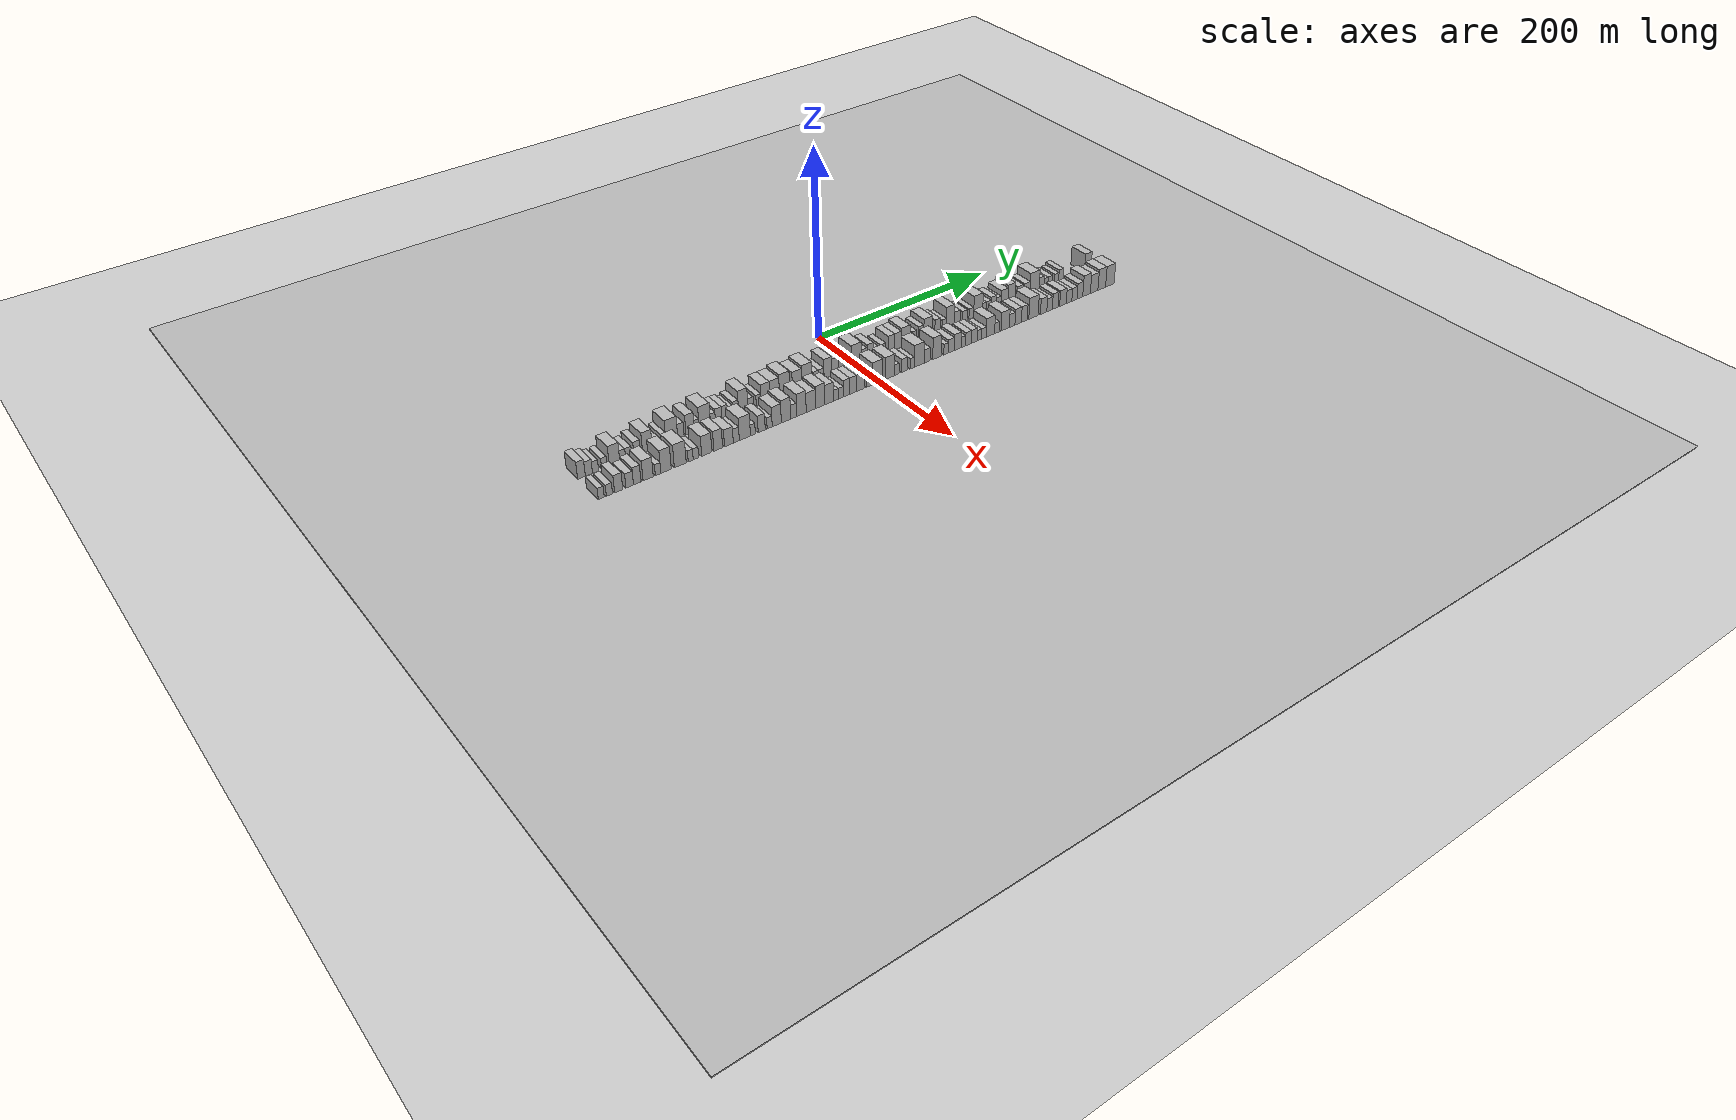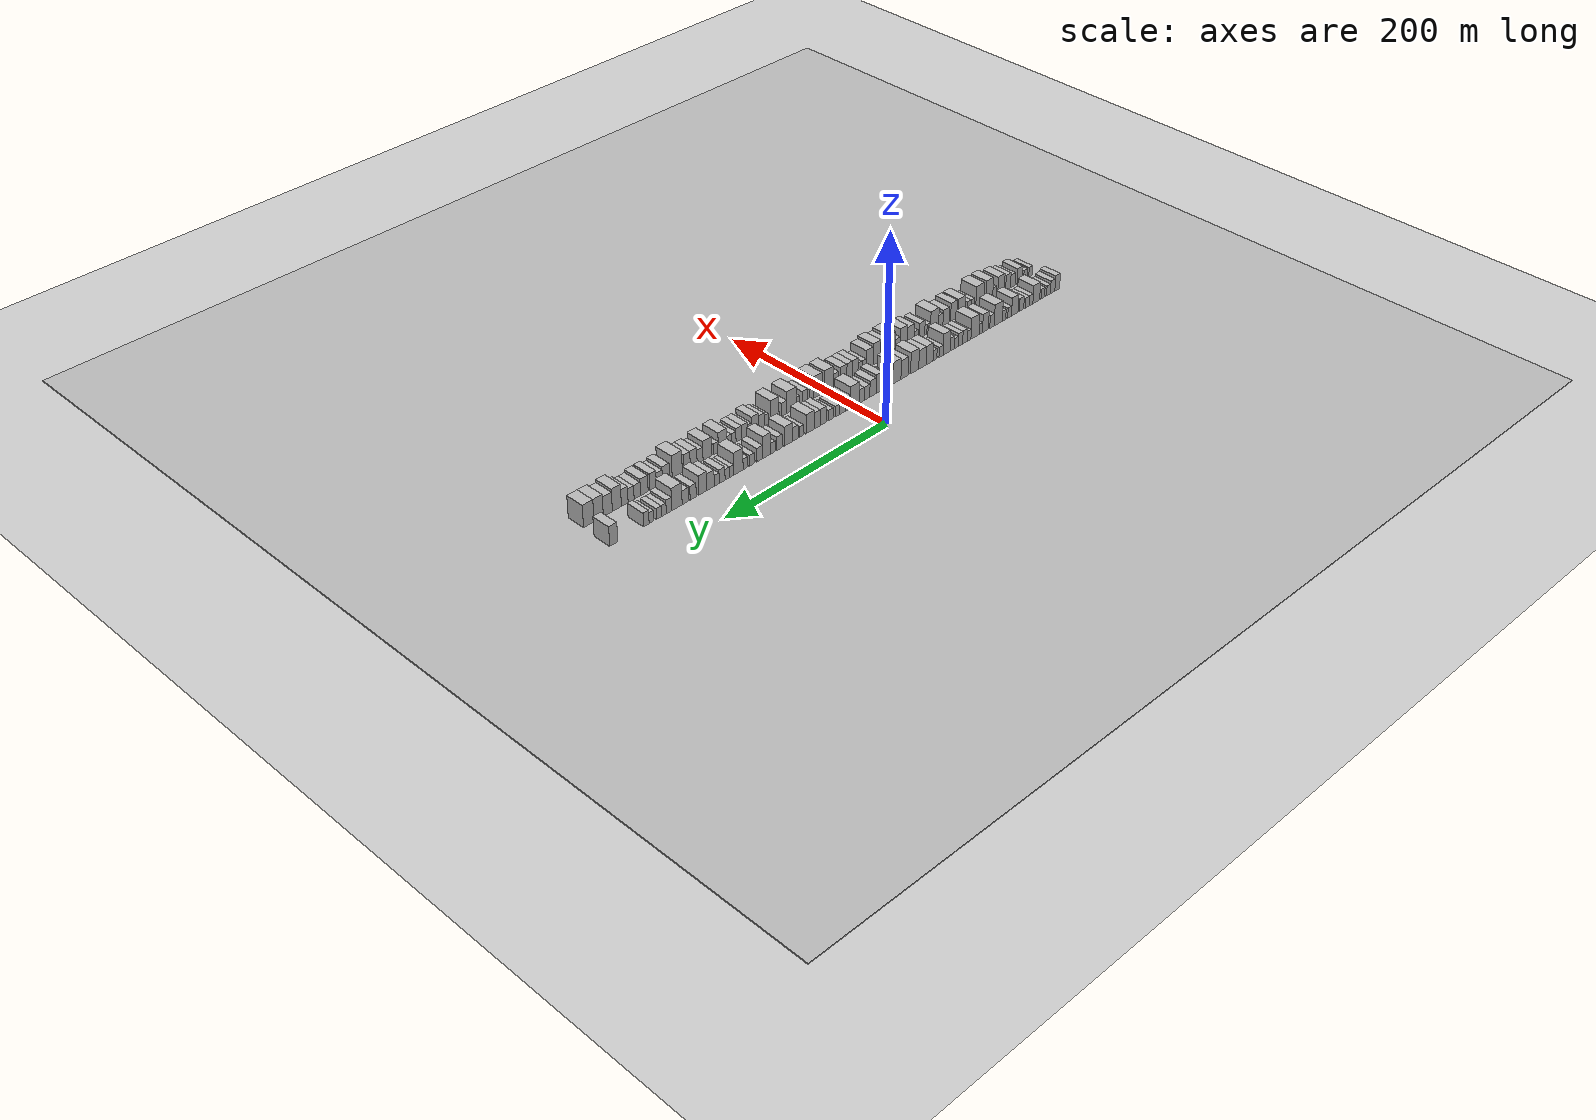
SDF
<?xml version="1.0" encoding="utf-8"?>

<sdf version="1.6">

   <world name="default">

      <gui fullscreen="0">

         <camera name="user_camera">

            <pose>-15 0 4.57585 0 0 0</pose>

            <view_controller>orbit</view_controller>

         </camera>

      </gui>

      <scene>

         <sky>

           <clouds>

             <speed>12</speed>

           </clouds>

         </sky>

         <ambient>0.4 0.4 0.4 1</ambient>

         <background>0.7 0.7 0.7 1</background>

         <shadows>1</shadows>

      </scene>

      <gravity>0 0 -9.8066</gravity>

      <magnetic_field>6e-06 2.3e-05 -4.2e-05</magnetic_field>

      <physics default="0" name="default_physics" type="ode">

         <ode>

            <solver>

               <type>quick</type>

               <iters>10</iters>

               <sor>1.0</sor>

               <use_dynamic_moi_rescaling>0</use_dynamic_moi_rescaling>

            </solver>

            <constraints>

               <cfm>0</cfm>

               <erp>0.2</erp>

               <contact_max_correcting_vel>100</contact_max_correcting_vel>

               <contact_surface_layer>0.001</contact_surface_layer>

            </constraints>

         </ode>

         <max_step_size>0.004</max_step_size>

         <real_time_factor>1</real_time_factor>

         <real_time_update_rate>250</real_time_update_rate>

      </physics>

      <light name="sun" type="directional">

         <cast_shadows>1</cast_shadows>

         <pose>0 0 10 0 0 0</pose>

         <diffuse>0.8 0.8 0.8 1</diffuse>

         <specular>0.2 0.2 0.2 1</specular>

         <attenuation>

            <range>1000</range>

            <constant>0.9</constant>

            <linear>0.01</linear>

            <quadratic>0.001</quadratic>

         </attenuation>

         <direction>-0.5 0.1 -0.9</direction>

      </light>

      <include>

         <name>ground_plane_1</name>

         <uri>model://HANNAS_ground_plane</uri>

         <pose>0 0 0  0 0 0</pose>

      </include>

      <include>

         <name>ground_plane_2</name>

         <uri>model://HANNAS_ground_plane</uri>

         <pose>100 0 0  0 0 0</pose>

      </include>

      <model name="building_1">

         <static>1</static>

         <pose frame="">50.0000 -286.3895 0 0.000000 0.000000 0.000000</pose>

         <link name="link">

            <pose frame="">0 0 9.00 0 0 0</pose>

            <collision name="collision">

               <geometry>

                  <box>

                     <size>20.0000 7.2210 18.0000</size>

                  </box>

               </geometry>

               <max_contacts>10</max_contacts>

               <surface>

                  <contact>

                     <ode/>

                  </contact>

                  <bounce/>

                  <friction>

                     <torsional>

                        <ode/>

                     </torsional>

                     <ode/>

                  </friction>

               </surface>

            </collision>

            <visual name="visual">

               <cast_shadows>0</cast_shadows>

               <geometry>

                  <box>

                     <size>20.0000 7.2210 18.0000</size>

                  </box>

               </geometry>

               <material>

                  <script>

                     <uri>model://HANNAS_wall/materials/scripts</uri>

                     <uri>model://HANNAS_wall/materials/textures</uri>

                     <name>vrc/HANNAS_wall</name>

                  </script>

               </material>

            </visual>

            <self_collide>0</self_collide>

            <enable_wind>0</enable_wind>

            <kinematic>0</kinematic>

         </link>

      </model>

      <model name="building_2">

         <static>1</static>

         <pose frame="">50.0000 -279.3729 0 0.000000 0.000000 0.000000</pose>

         <link name="link">

            <pose frame="">0 0 7.50 0 0 0</pose>

            <collision name="collision">

               <geometry>

                  <box>

                     <size>20.0000 6.8122 15.0000</size>

                  </box>

               </geometry>

               <max_contacts>10</max_contacts>

               <surface>

                  <contact>

                     <ode/>

                  </contact>

                  <bounce/>

                  <friction>

                     <torsional>

                        <ode/>

                     </torsional>

                     <ode/>

                  </friction>

               </surface>

            </collision>

            <visual name="visual">

               <cast_shadows>0</cast_shadows>

               <geometry>

                  <box>

                     <size>20.0000 6.8122 15.0000</size>

                  </box>

               </geometry>

               <material>

                  <script>

                     <uri>model://HANNAS_wall/materials/scripts</uri>

                     <uri>model://HANNAS_wall/materials/textures</uri>

                     <name>vrc/HANNAS_wall</name>

                  </script>

               </material>

            </visual>

            <self_collide>0</self_collide>

            <enable_wind>0</enable_wind>

            <kinematic>0</kinematic>

         </link>

      </model>

      <model name="building_3">

         <static>1</static>

         <pose frame="">50.0000 -273.0551 0 0.000000 0.000000 0.000000</pose>

         <link name="link">

            <pose frame="">0 0 6.00 0 0 0</pose>

            <collision name="collision">

               <geometry>

                  <box>

                     <size>20.0000 5.8235 12.0000</size>

                  </box>

               </geometry>

               <max_contacts>10</max_contacts>

               <surface>

                  <contact>

                     <ode/>

                  </contact>

                  <bounce/>

                  <friction>

                     <torsional>

                        <ode/>

                     </torsional>

                     <ode/>

                  </friction>

               </surface>

            </collision>

            <visual name="visual">

               <cast_shadows>0</cast_shadows>

               <geometry>

                  <box>

                     <size>20.0000 5.8235 12.0000</size>

                  </box>

               </geometry>

               <material>

                  <script>

                     <uri>model://HANNAS_wall/materials/scripts</uri>

                     <uri>model://HANNAS_wall/materials/textures</uri>

                     <name>vrc/HANNAS_wall</name>

                  </script>

               </material>

            </visual>

            <self_collide>0</self_collide>

            <enable_wind>0</enable_wind>

            <kinematic>0</kinematic>

         </link>

      </model>

      <model name="building_4">

         <static>1</static>

         <pose frame="">50.0000 -264.4733 0 0.000000 0.000000 0.000000</pose>

         <link name="link">

            <pose frame="">0 0 6.00 0 0 0</pose>

            <collision name="collision">

               <geometry>

                  <box>

                     <size>20.0000 5.3401 12.0000</size>

                  </box>

               </geometry>

               <max_contacts>10</max_contacts>

               <surface>

                  <contact>

                     <ode/>

                  </contact>

                  <bounce/>

                  <friction>

                     <torsional>

                        <ode/>

                     </torsional>

                     <ode/>

                  </friction>

               </surface>

            </collision>

            <visual name="visual">

               <cast_shadows>0</cast_shadows>

               <geometry>

                  <box>

                     <size>20.0000 5.3401 12.0000</size>

                  </box>

               </geometry>

               <material>

                  <script>

                     <uri>model://HANNAS_wall/materials/scripts</uri>

                     <uri>model://HANNAS_wall/materials/textures</uri>

                     <name>vrc/HANNAS_wall</name>

                  </script>

               </material>

            </visual>

            <self_collide>0</self_collide>

            <enable_wind>0</enable_wind>

            <kinematic>0</kinematic>

         </link>

      </model>

      <model name="building_5">

         <static>1</static>

         <pose frame="">50.0000 -254.7529 0 0.000000 0.000000 0.000000</pose>

         <link name="link">

            <pose frame="">0 0 10.50 0 0 0</pose>

            <collision name="collision">

               <geometry>

                  <box>

                     <size>20.0000 10.1005 21.0000</size>

                  </box>

               </geometry>

               <max_contacts>10</max_contacts>

               <surface>

                  <contact>

                     <ode/>

                  </contact>

                  <bounce/>

                  <friction>

                     <torsional>

                        <ode/>

                     </torsional>

                     <ode/>

                  </friction>

               </surface>

            </collision>

            <visual name="visual">

               <cast_shadows>0</cast_shadows>

               <geometry>

                  <box>

                     <size>20.0000 10.1005 21.0000</size>

                  </box>

               </geometry>

               <material>

                  <script>

                     <uri>model://HANNAS_wall/materials/scripts</uri>

                     <uri>model://HANNAS_wall/materials/textures</uri>

                     <name>vrc/HANNAS_wall</name>

                  </script>

               </material>

            </visual>

            <self_collide>0</self_collide>

            <enable_wind>0</enable_wind>

            <kinematic>0</kinematic>

         </link>

      </model>

      <model name="building_6">

         <static>1</static>

         <pose frame="">50.0000 -246.8271 0 0.000000 0.000000 0.000000</pose>

         <link name="link">

            <pose frame="">0 0 6.00 0 0 0</pose>

            <collision name="collision">

               <geometry>

                  <box>

                     <size>20.0000 5.7511 12.0000</size>

                  </box>

               </geometry>

               <max_contacts>10</max_contacts>

               <surface>

                  <contact>

                     <ode/>

                  </contact>

                  <bounce/>

                  <friction>

                     <torsional>

                        <ode/>

                     </torsional>

                     <ode/>

                  </friction>

               </surface>

            </collision>

            <visual name="visual">

               <cast_shadows>0</cast_shadows>

               <geometry>

                  <box>

                     <size>20.0000 5.7511 12.0000</size>

                  </box>

               </geometry>

               <material>

                  <script>

                     <uri>model://HANNAS_wall/materials/scripts</uri>

                     <uri>model://HANNAS_wall/materials/textures</uri>

                     <name>vrc/HANNAS_wall</name>

                  </script>

               </material>

            </visual>

            <self_collide>0</self_collide>

            <enable_wind>0</enable_wind>

            <kinematic>0</kinematic>

         </link>

      </model>

      <model name="building_7">

         <static>1</static>

         <pose frame="">50.0000 -240.9666 0 0.000000 0.000000 0.000000</pose>

         <link name="link">

            <pose frame="">0 0 6.00 0 0 0</pose>

            <collision name="collision">

               <geometry>

                  <box>

                     <size>20.0000 5.9700 12.0000</size>

                  </box>

               </geometry>

               <max_contacts>10</max_contacts>

               <surface>

                  <contact>

                     <ode/>

                  </contact>

                  <bounce/>

                  <friction>

                     <torsional>

                        <ode/>

                     </torsional>

                     <ode/>

                  </friction>

               </surface>

            </collision>

            <visual name="visual">

               <cast_shadows>0</cast_shadows>

               <geometry>

                  <box>

                     <size>20.0000 5.9700 12.0000</size>

                  </box>

               </geometry>

               <material>

                  <script>

                     <uri>model://HANNAS_wall/materials/scripts</uri>

                     <uri>model://HANNAS_wall/materials/textures</uri>

                     <name>vrc/HANNAS_wall</name>

                  </script>

               </material>

            </visual>

            <self_collide>0</self_collide>

            <enable_wind>0</enable_wind>

            <kinematic>0</kinematic>

         </link>

      </model>

      <model name="building_8">

         <static>1</static>

         <pose frame="">50.0000 -232.7494 0 0.000000 0.000000 0.000000</pose>

         <link name="link">

            <pose frame="">0 0 7.50 0 0 0</pose>

            <collision name="collision">

               <geometry>

                  <box>

                     <size>20.0000 6.4645 15.0000</size>

                  </box>

               </geometry>

               <max_contacts>10</max_contacts>

               <surface>

                  <contact>

                     <ode/>

                  </contact>

                  <bounce/>

                  <friction>

                     <torsional>

                        <ode/>

                     </torsional>

                     <ode/>

                  </friction>

               </surface>

            </collision>

            <visual name="visual">

               <cast_shadows>0</cast_shadows>

               <geometry>

                  <box>

                     <size>20.0000 6.4645 15.0000</size>

                  </box>

               </geometry>

               <material>

                  <script>

                     <uri>model://HANNAS_wall/materials/scripts</uri>

                     <uri>model://HANNAS_wall/materials/textures</uri>

                     <name>vrc/HANNAS_wall</name>

                  </script>

               </material>

            </visual>

            <self_collide>0</self_collide>

            <enable_wind>0</enable_wind>

            <kinematic>0</kinematic>

         </link>

      </model>

      <model name="building_9">

         <static>1</static>

         <pose frame="">50.0000 -222.6896 0 0.000000 0.000000 0.000000</pose>

         <link name="link">

            <pose frame="">0 0 10.50 0 0 0</pose>

            <collision name="collision">

               <geometry>

                  <box>

                     <size>20.0000 9.6550 21.0000</size>

                  </box>

               </geometry>

               <max_contacts>10</max_contacts>

               <surface>

                  <contact>

                     <ode/>

                  </contact>

                  <bounce/>

                  <friction>

                     <torsional>

                        <ode/>

                     </torsional>

                     <ode/>

                  </friction>

               </surface>

            </collision>

            <visual name="visual">

               <cast_shadows>0</cast_shadows>

               <geometry>

                  <box>

                     <size>20.0000 9.6550 21.0000</size>

                  </box>

               </geometry>

               <material>

                  <script>

                     <uri>model://HANNAS_wall/materials/scripts</uri>

                     <uri>model://HANNAS_wall/materials/textures</uri>

                     <name>vrc/HANNAS_wall</name>

                  </script>

               </material>

            </visual>

            <self_collide>0</self_collide>

            <enable_wind>0</enable_wind>

            <kinematic>0</kinematic>

         </link>

      </model>

      <model name="building_10">

         <static>1</static>

         <pose frame="">50.0000 -215.1177 0 0.000000 0.000000 0.000000</pose>

         <link name="link">

            <pose frame="">0 0 6.00 0 0 0</pose>

            <collision name="collision">

               <geometry>

                  <box>

                     <size>20.0000 5.4889 12.0000</size>

                  </box>

               </geometry>

               <max_contacts>10</max_contacts>

               <surface>

                  <contact>

                     <ode/>

                  </contact>

                  <bounce/>

                  <friction>

                     <torsional>

                        <ode/>

                     </torsional>

                     <ode/>

                  </friction>

               </surface>

            </collision>

            <visual name="visual">

               <cast_shadows>0</cast_shadows>

               <geometry>

                  <box>

                     <size>20.0000 5.4889 12.0000</size>

                  </box>

               </geometry>

               <material>

                  <script>

                     <uri>model://HANNAS_wall/materials/scripts</uri>

                     <uri>model://HANNAS_wall/materials/textures</uri>

                     <name>vrc/HANNAS_wall</name>

                  </script>

               </material>

            </visual>

            <self_collide>0</self_collide>

            <enable_wind>0</enable_wind>

            <kinematic>0</kinematic>

         </link>

      </model>

      <model name="building_11">

         <static>1</static>

         <pose frame="">50.0000 -206.8450 0 0.000000 0.000000 0.000000</pose>

         <link name="link">

            <pose frame="">0 0 6.00 0 0 0</pose>

            <collision name="collision">

               <geometry>

                  <box>

                     <size>20.0000 5.0564 12.0000</size>

                  </box>

               </geometry>

               <max_contacts>10</max_contacts>

               <surface>

                  <contact>

                     <ode/>

                  </contact>

                  <bounce/>

                  <friction>

                     <torsional>

                        <ode/>

                     </torsional>

                     <ode/>

                  </friction>

               </surface>

            </collision>

            <visual name="visual">

               <cast_shadows>0</cast_shadows>

               <geometry>

                  <box>

                     <size>20.0000 5.0564 12.0000</size>

                  </box>

               </geometry>

               <material>

                  <script>

                     <uri>model://HANNAS_wall/materials/scripts</uri>

                     <uri>model://HANNAS_wall/materials/textures</uri>

                     <name>vrc/HANNAS_wall</name>

                  </script>

               </material>

            </visual>

            <self_collide>0</self_collide>

            <enable_wind>0</enable_wind>

            <kinematic>0</kinematic>

         </link>

      </model>

      <model name="building_12">

         <static>1</static>

         <pose frame="">50.0000 -198.4325 0 0.000000 0.000000 0.000000</pose>

         <link name="link">

            <pose frame="">0 0 12.00 0 0 0</pose>

            <collision name="collision">

               <geometry>

                  <box>

                     <size>20.0000 11.7688 24.0000</size>

                  </box>

               </geometry>

               <max_contacts>10</max_contacts>

               <surface>

                  <contact>

                     <ode/>

                  </contact>

                  <bounce/>

                  <friction>

                     <torsional>

                        <ode/>

                     </torsional>

                     <ode/>

                  </friction>

               </surface>

            </collision>

            <visual name="visual">

               <cast_shadows>0</cast_shadows>

               <geometry>

                  <box>

                     <size>20.0000 11.7688 24.0000</size>

                  </box>

               </geometry>

               <material>

                  <script>

                     <uri>model://HANNAS_wall/materials/scripts</uri>

                     <uri>model://HANNAS_wall/materials/textures</uri>

                     <name>vrc/HANNAS_wall</name>

                  </script>

               </material>

            </visual>

            <self_collide>0</self_collide>

            <enable_wind>0</enable_wind>

            <kinematic>0</kinematic>

         </link>

      </model>

      <model name="building_13">

         <static>1</static>

         <pose frame="">50.0000 -189.3701 0 0.000000 0.000000 0.000000</pose>

         <link name="link">

            <pose frame="">0 0 7.50 0 0 0</pose>

            <collision name="collision">

               <geometry>

                  <box>

                     <size>20.0000 6.3559 15.0000</size>

                  </box>

               </geometry>

               <max_contacts>10</max_contacts>

               <surface>

                  <contact>

                     <ode/>

                  </contact>

                  <bounce/>

                  <friction>

                     <torsional>

                        <ode/>

                     </torsional>

                     <ode/>

                  </friction>

               </surface>

            </collision>

            <visual name="visual">

               <cast_shadows>0</cast_shadows>

               <geometry>

                  <box>

                     <size>20.0000 6.3559 15.0000</size>

                  </box>

               </geometry>

               <material>

                  <script>

                     <uri>model://HANNAS_wall/materials/scripts</uri>

                     <uri>model://HANNAS_wall/materials/textures</uri>

                     <name>vrc/HANNAS_wall</name>

                  </script>

               </material>

            </visual>

            <self_collide>0</self_collide>

            <enable_wind>0</enable_wind>

            <kinematic>0</kinematic>

         </link>

      </model>

      <model name="building_14">

         <static>1</static>

         <pose frame="">50.0000 -179.9469 0 0.000000 0.000000 0.000000</pose>

         <link name="link">

            <pose frame="">0 0 10.50 0 0 0</pose>

            <collision name="collision">

               <geometry>

                  <box>

                     <size>20.0000 8.4906 21.0000</size>

                  </box>

               </geometry>

               <max_contacts>10</max_contacts>

               <surface>

                  <contact>

                     <ode/>

                  </contact>

                  <bounce/>

                  <friction>

                     <torsional>

                        <ode/>

                     </torsional>

                     <ode/>

                  </friction>

               </surface>

            </collision>

            <visual name="visual">

               <cast_shadows>0</cast_shadows>

               <geometry>

                  <box>

                     <size>20.0000 8.4906 21.0000</size>

                  </box>

               </geometry>

               <material>

                  <script>

                     <uri>model://HANNAS_wall/materials/scripts</uri>

                     <uri>model://HANNAS_wall/materials/textures</uri>

                     <name>vrc/HANNAS_wall</name>

                  </script>

               </material>

            </visual>

            <self_collide>0</self_collide>

            <enable_wind>0</enable_wind>

            <kinematic>0</kinematic>

         </link>

      </model>

      <model name="building_15">

         <static>1</static>

         <pose frame="">50.0000 -173.2191 0 0.000000 0.000000 0.000000</pose>

         <link name="link">

            <pose frame="">0 0 6.00 0 0 0</pose>

            <collision name="collision">

               <geometry>

                  <box>

                     <size>20.0000 4.9650 12.0000</size>

                  </box>

               </geometry>

               <max_contacts>10</max_contacts>

               <surface>

                  <contact>

                     <ode/>

                  </contact>

                  <bounce/>

                  <friction>

                     <torsional>

                        <ode/>

                     </torsional>

                     <ode/>

                  </friction>

               </surface>

            </collision>

            <visual name="visual">

               <cast_shadows>0</cast_shadows>

               <geometry>

                  <box>

                     <size>20.0000 4.9650 12.0000</size>

                  </box>

               </geometry>

               <material>

                  <script>

                     <uri>model://HANNAS_wall/materials/scripts</uri>

                     <uri>model://HANNAS_wall/materials/textures</uri>

                     <name>vrc/HANNAS_wall</name>

                  </script>

               </material>

            </visual>

            <self_collide>0</self_collide>

            <enable_wind>0</enable_wind>

            <kinematic>0</kinematic>

         </link>

      </model>

      <model name="building_16">

         <static>1</static>

         <pose frame="">50.0000 -164.9299 0 0.000000 0.000000 0.000000</pose>

         <link name="link">

            <pose frame="">0 0 12.00 0 0 0</pose>

            <collision name="collision">

               <geometry>

                  <box>

                     <size>20.0000 11.6135 24.0000</size>

                  </box>

               </geometry>

               <max_contacts>10</max_contacts>

               <surface>

                  <contact>

                     <ode/>

                  </contact>

                  <bounce/>

                  <friction>

                     <torsional>

                        <ode/>

                     </torsional>

                     <ode/>

                  </friction>

               </surface>

            </collision>

            <visual name="visual">

               <cast_shadows>0</cast_shadows>

               <geometry>

                  <box>

                     <size>20.0000 11.6135 24.0000</size>

                  </box>

               </geometry>

               <material>

                  <script>

                     <uri>model://HANNAS_wall/materials/scripts</uri>

                     <uri>model://HANNAS_wall/materials/textures</uri>

                     <name>vrc/HANNAS_wall</name>

                  </script>

               </material>

            </visual>

            <self_collide>0</self_collide>

            <enable_wind>0</enable_wind>

            <kinematic>0</kinematic>

         </link>

      </model>

      <model name="building_17">

         <static>1</static>

         <pose frame="">50.0000 -156.5490 0 0.000000 0.000000 0.000000</pose>

         <link name="link">

            <pose frame="">0 0 6.00 0 0 0</pose>

            <collision name="collision">

               <geometry>

                  <box>

                     <size>20.0000 5.1484 12.0000</size>

                  </box>

               </geometry>

               <max_contacts>10</max_contacts>

               <surface>

                  <contact>

                     <ode/>

                  </contact>

                  <bounce/>

                  <friction>

                     <torsional>

                        <ode/>

                     </torsional>

                     <ode/>

                  </friction>

               </surface>

            </collision>

            <visual name="visual">

               <cast_shadows>0</cast_shadows>

               <geometry>

                  <box>

                     <size>20.0000 5.1484 12.0000</size>

                  </box>

               </geometry>

               <material>

                  <script>

                     <uri>model://HANNAS_wall/materials/scripts</uri>

                     <uri>model://HANNAS_wall/materials/textures</uri>

                     <name>vrc/HANNAS_wall</name>

                  </script>

               </material>

            </visual>

            <self_collide>0</self_collide>

            <enable_wind>0</enable_wind>

            <kinematic>0</kinematic>

         </link>

      </model>

      <model name="building_18">

         <static>1</static>

         <pose frame="">50.0000 -150.6503 0 0.000000 0.000000 0.000000</pose>

         <link name="link">

            <pose frame="">0 0 7.50 0 0 0</pose>

            <collision name="collision">

               <geometry>

                  <box>

                     <size>20.0000 6.6490 15.0000</size>

                  </box>

               </geometry>

               <max_contacts>10</max_contacts>

               <surface>

                  <contact>

                     <ode/>

                  </contact>

                  <bounce/>

                  <friction>

                     <torsional>

                        <ode/>

                     </torsional>

                     <ode/>

                  </friction>

               </surface>

            </collision>

            <visual name="visual">

               <cast_shadows>0</cast_shadows>

               <geometry>

                  <box>

                     <size>20.0000 6.6490 15.0000</size>

                  </box>

               </geometry>

               <material>

                  <script>

                     <uri>model://HANNAS_wall/materials/scripts</uri>

                     <uri>model://HANNAS_wall/materials/textures</uri>

                     <name>vrc/HANNAS_wall</name>

                  </script>

               </material>

            </visual>

            <self_collide>0</self_collide>

            <enable_wind>0</enable_wind>

            <kinematic>0</kinematic>

         </link>

      </model>

      <model name="building_19">

         <static>1</static>

         <pose frame="">50.0000 -144.2925 0 0.000000 0.000000 0.000000</pose>

         <link name="link">

            <pose frame="">0 0 7.50 0 0 0</pose>

            <collision name="collision">

               <geometry>

                  <box>

                     <size>20.0000 6.0666 15.0000</size>

                  </box>

               </geometry>

               <max_contacts>10</max_contacts>

               <surface>

                  <contact>

                     <ode/>

                  </contact>

                  <bounce/>

                  <friction>

                     <torsional>

                        <ode/>

                     </torsional>

                     <ode/>

                  </friction>

               </surface>

            </collision>

            <visual name="visual">

               <cast_shadows>0</cast_shadows>

               <geometry>

                  <box>

                     <size>20.0000 6.0666 15.0000</size>

                  </box>

               </geometry>

               <material>

                  <script>

                     <uri>model://HANNAS_wall/materials/scripts</uri>

                     <uri>model://HANNAS_wall/materials/textures</uri>

                     <name>vrc/HANNAS_wall</name>

                  </script>

               </material>

            </visual>

            <self_collide>0</self_collide>

            <enable_wind>0</enable_wind>

            <kinematic>0</kinematic>

         </link>

      </model>

      <model name="building_20">

         <static>1</static>

         <pose frame="">50.0000 -138.5595 0 0.000000 0.000000 0.000000</pose>

         <link name="link">

            <pose frame="">0 0 6.00 0 0 0</pose>

            <collision name="collision">

               <geometry>

                  <box>

                     <size>20.0000 5.3994 12.0000</size>

                  </box>

               </geometry>

               <max_contacts>10</max_contacts>

               <surface>

                  <contact>

                     <ode/>

                  </contact>

                  <bounce/>

                  <friction>

                     <torsional>

                        <ode/>

                     </torsional>

                     <ode/>

                  </friction>

               </surface>

            </collision>

            <visual name="visual">

               <cast_shadows>0</cast_shadows>

               <geometry>

                  <box>

                     <size>20.0000 5.3994 12.0000</size>

                  </box>

               </geometry>

               <material>

                  <script>

                     <uri>model://HANNAS_wall/materials/scripts</uri>

                     <uri>model://HANNAS_wall/materials/textures</uri>

                     <name>vrc/HANNAS_wall</name>

                  </script>

               </material>

            </visual>

            <self_collide>0</self_collide>

            <enable_wind>0</enable_wind>

            <kinematic>0</kinematic>

         </link>

      </model>

      <model name="building_21">

         <static>1</static>

         <pose frame="">50.0000 -132.8455 0 0.000000 0.000000 0.000000</pose>

         <link name="link">

            <pose frame="">0 0 7.50 0 0 0</pose>

            <collision name="collision">

               <geometry>

                  <box>

                     <size>20.0000 6.0286 15.0000</size>

                  </box>

               </geometry>

               <max_contacts>10</max_contacts>

               <surface>

                  <contact>

                     <ode/>

                  </contact>

                  <bounce/>

                  <friction>

                     <torsional>

                        <ode/>

                     </torsional>

                     <ode/>

                  </friction>

               </surface>

            </collision>

            <visual name="visual">

               <cast_shadows>0</cast_shadows>

               <geometry>

                  <box>

                     <size>20.0000 6.0286 15.0000</size>

                  </box>

               </geometry>

               <material>

                  <script>

                     <uri>model://HANNAS_wall/materials/scripts</uri>

                     <uri>model://HANNAS_wall/materials/textures</uri>

                     <name>vrc/HANNAS_wall</name>

                  </script>

               </material>

            </visual>

            <self_collide>0</self_collide>

            <enable_wind>0</enable_wind>

            <kinematic>0</kinematic>

         </link>

      </model>

      <model name="building_22">

         <static>1</static>

         <pose frame="">50.0000 -124.9020 0 0.000000 0.000000 0.000000</pose>

         <link name="link">

            <pose frame="">0 0 12.00 0 0 0</pose>

            <collision name="collision">

               <geometry>

                  <box>

                     <size>20.0000 9.8583 24.0000</size>

                  </box>

               </geometry>

               <max_contacts>10</max_contacts>

               <surface>

                  <contact>

                     <ode/>

                  </contact>

                  <bounce/>

                  <friction>

                     <torsional>

                        <ode/>

                     </torsional>

                     <ode/>

                  </friction>

               </surface>

            </collision>

            <visual name="visual">

               <cast_shadows>0</cast_shadows>

               <geometry>

                  <box>

                     <size>20.0000 9.8583 24.0000</size>

                  </box>

               </geometry>

               <material>

                  <script>

                     <uri>model://HANNAS_wall/materials/scripts</uri>

                     <uri>model://HANNAS_wall/materials/textures</uri>

                     <name>vrc/HANNAS_wall</name>

                  </script>

               </material>

            </visual>

            <self_collide>0</self_collide>

            <enable_wind>0</enable_wind>

            <kinematic>0</kinematic>

         </link>

      </model>

      <model name="building_23">

         <static>1</static>

         <pose frame="">50.0000 -117.0329 0 0.000000 0.000000 0.000000</pose>

         <link name="link">

            <pose frame="">0 0 6.00 0 0 0</pose>

            <collision name="collision">

               <geometry>

                  <box>

                     <size>20.0000 5.8799 12.0000</size>

                  </box>

               </geometry>

               <max_contacts>10</max_contacts>

               <surface>

                  <contact>

                     <ode/>

                  </contact>

                  <bounce/>

                  <friction>

                     <torsional>

                        <ode/>

                     </torsional>

                     <ode/>

                  </friction>

               </surface>

            </collision>

            <visual name="visual">

               <cast_shadows>0</cast_shadows>

               <geometry>

                  <box>

                     <size>20.0000 5.8799 12.0000</size>

                  </box>

               </geometry>

               <material>

                  <script>

                     <uri>model://HANNAS_wall/materials/scripts</uri>

                     <uri>model://HANNAS_wall/materials/textures</uri>

                     <name>vrc/HANNAS_wall</name>

                  </script>

               </material>

            </visual>

            <self_collide>0</self_collide>

            <enable_wind>0</enable_wind>

            <kinematic>0</kinematic>

         </link>

      </model>

      <model name="building_24">

         <static>1</static>

         <pose frame="">50.0000 -108.4351 0 0.000000 0.000000 0.000000</pose>

         <link name="link">

            <pose frame="">0 0 6.00 0 0 0</pose>

            <collision name="collision">

               <geometry>

                  <box>

                     <size>20.0000 5.3156 12.0000</size>

                  </box>

               </geometry>

               <max_contacts>10</max_contacts>

               <surface>

                  <contact>

                     <ode/>

                  </contact>

                  <bounce/>

                  <friction>

                     <torsional>

                        <ode/>

                     </torsional>

                     <ode/>

                  </friction>

               </surface>

            </collision>

            <visual name="visual">

               <cast_shadows>0</cast_shadows>

               <geometry>

                  <box>

                     <size>20.0000 5.3156 12.0000</size>

                  </box>

               </geometry>

               <material>

                  <script>

                     <uri>model://HANNAS_wall/materials/scripts</uri>

                     <uri>model://HANNAS_wall/materials/textures</uri>

                     <name>vrc/HANNAS_wall</name>

                  </script>

               </material>

            </visual>

            <self_collide>0</self_collide>

            <enable_wind>0</enable_wind>

            <kinematic>0</kinematic>

         </link>

      </model>

      <model name="building_25">

         <static>1</static>

         <pose frame="">50.0000 -101.0850 0 0.000000 0.000000 0.000000</pose>

         <link name="link">

            <pose frame="">0 0 10.50 0 0 0</pose>

            <collision name="collision">

               <geometry>

                  <box>

                     <size>20.0000 9.3847 21.0000</size>

                  </box>

               </geometry>

               <max_contacts>10</max_contacts>

               <surface>

                  <contact>

                     <ode/>

                  </contact>

                  <bounce/>

                  <friction>

                     <torsional>

                        <ode/>

                     </torsional>

                     <ode/>

                  </friction>

               </surface>

            </collision>

            <visual name="visual">

               <cast_shadows>0</cast_shadows>

               <geometry>

                  <box>

                     <size>20.0000 9.3847 21.0000</size>

                  </box>

               </geometry>

               <material>

                  <script>

                     <uri>model://HANNAS_wall/materials/scripts</uri>

                     <uri>model://HANNAS_wall/materials/textures</uri>

                     <name>vrc/HANNAS_wall</name>

                  </script>

               </material>

            </visual>

            <self_collide>0</self_collide>

            <enable_wind>0</enable_wind>

            <kinematic>0</kinematic>

         </link>

      </model>

      <model name="building_26">

         <static>1</static>

         <pose frame="">50.0000 -91.2807 0 0.000000 0.000000 0.000000</pose>

         <link name="link">

            <pose frame="">0 0 10.50 0 0 0</pose>

            <collision name="collision">

               <geometry>

                  <box>

                     <size>20.0000 10.2239 21.0000</size>

                  </box>

               </geometry>

               <max_contacts>10</max_contacts>

               <surface>

                  <contact>

                     <ode/>

                  </contact>

                  <bounce/>

                  <friction>

                     <torsional>

                        <ode/>

                     </torsional>

                     <ode/>

                  </friction>

               </surface>

            </collision>

            <visual name="visual">

               <cast_shadows>0</cast_shadows>

               <geometry>

                  <box>

                     <size>20.0000 10.2239 21.0000</size>

                  </box>

               </geometry>

               <material>

                  <script>

                     <uri>model://HANNAS_wall/materials/scripts</uri>

                     <uri>model://HANNAS_wall/materials/textures</uri>

                     <name>vrc/HANNAS_wall</name>

                  </script>

               </material>

            </visual>

            <self_collide>0</self_collide>

            <enable_wind>0</enable_wind>

            <kinematic>0</kinematic>

         </link>

      </model>

      <model name="building_27">

         <static>1</static>

         <pose frame="">50.0000 -80.6186 0 0.000000 0.000000 0.000000</pose>

         <link name="link">

            <pose frame="">0 0 12.00 0 0 0</pose>

            <collision name="collision">

               <geometry>

                  <box>

                     <size>20.0000 11.1003 24.0000</size>

                  </box>

               </geometry>

               <max_contacts>10</max_contacts>

               <surface>

                  <contact>

                     <ode/>

                  </contact>

                  <bounce/>

                  <friction>

                     <torsional>

                        <ode/>

                     </torsional>

                     <ode/>

                  </friction>

               </surface>

            </collision>

            <visual name="visual">

               <cast_shadows>0</cast_shadows>

               <geometry>

                  <box>

                     <size>20.0000 11.1003 24.0000</size>

                  </box>

               </geometry>

               <material>

                  <script>

                     <uri>model://HANNAS_wall/materials/scripts</uri>

                     <uri>model://HANNAS_wall/materials/textures</uri>

                     <name>vrc/HANNAS_wall</name>

                  </script>

               </material>

            </visual>

            <self_collide>0</self_collide>

            <enable_wind>0</enable_wind>

            <kinematic>0</kinematic>

         </link>

      </model>

      <model name="building_28">

         <static>1</static>

         <pose frame="">50.0000 -66.9657 0 0.000000 0.000000 0.000000</pose>

         <link name="link">

            <pose frame="">0 0 10.50 0 0 0</pose>

            <collision name="collision">

               <geometry>

                  <box>

                     <size>20.0000 10.2054 21.0000</size>

                  </box>

               </geometry>

               <max_contacts>10</max_contacts>

               <surface>

                  <contact>

                     <ode/>

                  </contact>

                  <bounce/>

                  <friction>

                     <torsional>

                        <ode/>

                     </torsional>

                     <ode/>

                  </friction>

               </surface>

            </collision>

            <visual name="visual">

               <cast_shadows>0</cast_shadows>

               <geometry>

                  <box>

                     <size>20.0000 10.2054 21.0000</size>

                  </box>

               </geometry>

               <material>

                  <script>

                     <uri>model://HANNAS_wall/materials/scripts</uri>

                     <uri>model://HANNAS_wall/materials/textures</uri>

                     <name>vrc/HANNAS_wall</name>

                  </script>

               </material>

            </visual>

            <self_collide>0</self_collide>

            <enable_wind>0</enable_wind>

            <kinematic>0</kinematic>

         </link>

      </model>

      <model name="building_29">

         <static>1</static>

         <pose frame="">50.0000 -56.2812 0 0.000000 0.000000 0.000000</pose>

         <link name="link">

            <pose frame="">0 0 12.00 0 0 0</pose>

            <collision name="collision">

               <geometry>

                  <box>

                     <size>20.0000 11.1637 24.0000</size>

                  </box>

               </geometry>

               <max_contacts>10</max_contacts>

               <surface>

                  <contact>

                     <ode/>

                  </contact>

                  <bounce/>

                  <friction>

                     <torsional>

                        <ode/>

                     </torsional>

                     <ode/>

                  </friction>

               </surface>

            </collision>

            <visual name="visual">

               <cast_shadows>0</cast_shadows>

               <geometry>

                  <box>

                     <size>20.0000 11.1637 24.0000</size>

                  </box>

               </geometry>

               <material>

                  <script>

                     <uri>model://HANNAS_wall/materials/scripts</uri>

                     <uri>model://HANNAS_wall/materials/textures</uri>

                     <name>vrc/HANNAS_wall</name>

                  </script>

               </material>

            </visual>

            <self_collide>0</self_collide>

            <enable_wind>0</enable_wind>

            <kinematic>0</kinematic>

         </link>

      </model>

      <model name="building_30">

         <static>1</static>

         <pose frame="">50.0000 -45.8224 0 0.000000 0.000000 0.000000</pose>

         <link name="link">

            <pose frame="">0 0 6.00 0 0 0</pose>

            <collision name="collision">

               <geometry>

                  <box>

                     <size>20.0000 5.7540 12.0000</size>

                  </box>

               </geometry>

               <max_contacts>10</max_contacts>

               <surface>

                  <contact>

                     <ode/>

                  </contact>

                  <bounce/>

                  <friction>

                     <torsional>

                        <ode/>

                     </torsional>

                     <ode/>

                  </friction>

               </surface>

            </collision>

            <visual name="visual">

               <cast_shadows>0</cast_shadows>

               <geometry>

                  <box>

                     <size>20.0000 5.7540 12.0000</size>

                  </box>

               </geometry>

               <material>

                  <script>

                     <uri>model://HANNAS_wall/materials/scripts</uri>

                     <uri>model://HANNAS_wall/materials/textures</uri>

                     <name>vrc/HANNAS_wall</name>

                  </script>

               </material>

            </visual>

            <self_collide>0</self_collide>

            <enable_wind>0</enable_wind>

            <kinematic>0</kinematic>

         </link>

      </model>

      <model name="building_31">

         <static>1</static>

         <pose frame="">50.0000 -40.0100 0 0.000000 0.000000 0.000000</pose>

         <link name="link">

            <pose frame="">0 0 6.00 0 0 0</pose>

            <collision name="collision">

               <geometry>

                  <box>

                     <size>20.0000 5.8707 12.0000</size>

                  </box>

               </geometry>

               <max_contacts>10</max_contacts>

               <surface>

                  <contact>

                     <ode/>

                  </contact>

                  <bounce/>

                  <friction>

                     <torsional>

                        <ode/>

                     </torsional>

                     <ode/>

                  </friction>

               </surface>

            </collision>

            <visual name="visual">

               <cast_shadows>0</cast_shadows>

               <geometry>

                  <box>

                     <size>20.0000 5.8707 12.0000</size>

                  </box>

               </geometry>

               <material>

                  <script>

                     <uri>model://HANNAS_wall/materials/scripts</uri>

                     <uri>model://HANNAS_wall/materials/textures</uri>

                     <name>vrc/HANNAS_wall</name>

                  </script>

               </material>

            </visual>

            <self_collide>0</self_collide>

            <enable_wind>0</enable_wind>

            <kinematic>0</kinematic>

         </link>

      </model>

      <model name="building_32">

         <static>1</static>

         <pose frame="">50.0000 -32.7911 0 0.000000 0.000000 0.000000</pose>

         <link name="link">

            <pose frame="">0 0 10.50 0 0 0</pose>

            <collision name="collision">

               <geometry>

                  <box>

                     <size>20.0000 8.5672 21.0000</size>

                  </box>

               </geometry>

               <max_contacts>10</max_contacts>

               <surface>

                  <contact>

                     <ode/>

                  </contact>

                  <bounce/>

                  <friction>

                     <torsional>

                        <ode/>

                     </torsional>

                     <ode/>

                  </friction>

               </surface>

            </collision>

            <visual name="visual">

               <cast_shadows>0</cast_shadows>

               <geometry>

                  <box>

                     <size>20.0000 8.5672 21.0000</size>

                  </box>

               </geometry>

               <material>

                  <script>

                     <uri>model://HANNAS_wall/materials/scripts</uri>

                     <uri>model://HANNAS_wall/materials/textures</uri>

                     <name>vrc/HANNAS_wall</name>

                  </script>

               </material>

            </visual>

            <self_collide>0</self_collide>

            <enable_wind>0</enable_wind>

            <kinematic>0</kinematic>

         </link>

      </model>

      <model name="building_33">

         <static>1</static>

         <pose frame="">50.0000 -24.3727 0 0.000000 0.000000 0.000000</pose>

         <link name="link">

            <pose frame="">0 0 9.00 0 0 0</pose>

            <collision name="collision">

               <geometry>

                  <box>

                     <size>20.0000 8.2696 18.0000</size>

                  </box>

               </geometry>

               <max_contacts>10</max_contacts>

               <surface>

                  <contact>

                     <ode/>

                  </contact>

                  <bounce/>

                  <friction>

                     <torsional>

                        <ode/>

                     </torsional>

                     <ode/>

                  </friction>

               </surface>

            </collision>

            <visual name="visual">

               <cast_shadows>0</cast_shadows>

               <geometry>

                  <box>

                     <size>20.0000 8.2696 18.0000</size>

                  </box>

               </geometry>

               <material>

                  <script>

                     <uri>model://HANNAS_wall/materials/scripts</uri>

                     <uri>model://HANNAS_wall/materials/textures</uri>

                     <name>vrc/HANNAS_wall</name>

                  </script>

               </material>

            </visual>

            <self_collide>0</self_collide>

            <enable_wind>0</enable_wind>

            <kinematic>0</kinematic>

         </link>

      </model>

      <model name="building_34">

         <static>1</static>

         <pose frame="">50.0000 -16.6368 0 0.000000 0.000000 0.000000</pose>

         <link name="link">

            <pose frame="">0 0 7.50 0 0 0</pose>

            <collision name="collision">

               <geometry>

                  <box>

                     <size>20.0000 7.2022 15.0000</size>

                  </box>

               </geometry>

               <max_contacts>10</max_contacts>

               <surface>

                  <contact>

                     <ode/>

                  </contact>

                  <bounce/>

                  <friction>

                     <torsional>

                        <ode/>

                     </torsional>

                     <ode/>

                  </friction>

               </surface>

            </collision>

            <visual name="visual">

               <cast_shadows>0</cast_shadows>

               <geometry>

                  <box>

                     <size>20.0000 7.2022 15.0000</size>

                  </box>

               </geometry>

               <material>

                  <script>

                     <uri>model://HANNAS_wall/materials/scripts</uri>

                     <uri>model://HANNAS_wall/materials/textures</uri>

                     <name>vrc/HANNAS_wall</name>

                  </script>

               </material>

            </visual>

            <self_collide>0</self_collide>

            <enable_wind>0</enable_wind>

            <kinematic>0</kinematic>

         </link>

      </model>

      <model name="building_35">

         <static>1</static>

         <pose frame="">50.0000 -9.7083 0 0.000000 0.000000 0.000000</pose>

         <link name="link">

            <pose frame="">0 0 7.50 0 0 0</pose>

            <collision name="collision">

               <geometry>

                  <box>

                     <size>20.0000 6.6549 15.0000</size>

                  </box>

               </geometry>

               <max_contacts>10</max_contacts>

               <surface>

                  <contact>

                     <ode/>

                  </contact>

                  <bounce/>

                  <friction>

                     <torsional>

                        <ode/>

                     </torsional>

                     <ode/>

                  </friction>

               </surface>

            </collision>

            <visual name="visual">

               <cast_shadows>0</cast_shadows>

               <geometry>

                  <box>

                     <size>20.0000 6.6549 15.0000</size>

                  </box>

               </geometry>

               <material>

                  <script>

                     <uri>model://HANNAS_wall/materials/scripts</uri>

                     <uri>model://HANNAS_wall/materials/textures</uri>

                     <name>vrc/HANNAS_wall</name>

                  </script>

               </material>

            </visual>

            <self_collide>0</self_collide>

            <enable_wind>0</enable_wind>

            <kinematic>0</kinematic>

         </link>

      </model>

      <model name="building_36">

         <static>1</static>

         <pose frame="">50.0000 -0.5965 0 0.000000 0.000000 0.000000</pose>

         <link name="link">

            <pose frame="">0 0 12.00 0 0 0</pose>

            <collision name="collision">

               <geometry>

                  <box>

                     <size>20.0000 11.5688 24.0000</size>

                  </box>

               </geometry>

               <max_contacts>10</max_contacts>

               <surface>

                  <contact>

                     <ode/>

                  </contact>

                  <bounce/>

                  <friction>

                     <torsional>

                        <ode/>

                     </torsional>

                     <ode/>

                  </friction>

               </surface>

            </collision>

            <visual name="visual">

               <cast_shadows>0</cast_shadows>

               <geometry>

                  <box>

                     <size>20.0000 11.5688 24.0000</size>

                  </box>

               </geometry>

               <material>

                  <script>

                     <uri>model://HANNAS_wall/materials/scripts</uri>

                     <uri>model://HANNAS_wall/materials/textures</uri>

                     <name>vrc/HANNAS_wall</name>

                  </script>

               </material>

            </visual>

            <self_collide>0</self_collide>

            <enable_wind>0</enable_wind>

            <kinematic>0</kinematic>

         </link>

      </model>

      <model name="building_37">

         <static>1</static>

         <pose frame="">50.0000 8.4967 0 0.000000 0.000000 0.000000</pose>

         <link name="link">

            <pose frame="">0 0 7.50 0 0 0</pose>

            <collision name="collision">

               <geometry>

                  <box>

                     <size>20.0000 6.6175 15.0000</size>

                  </box>

               </geometry>

               <max_contacts>10</max_contacts>

               <surface>

                  <contact>

                     <ode/>

                  </contact>

                  <bounce/>

                  <friction>

                     <torsional>

                        <ode/>

                     </torsional>

                     <ode/>

                  </friction>

               </surface>

            </collision>

            <visual name="visual">

               <cast_shadows>0</cast_shadows>

               <geometry>

                  <box>

                     <size>20.0000 6.6175 15.0000</size>

                  </box>

               </geometry>

               <material>

                  <script>

                     <uri>model://HANNAS_wall/materials/scripts</uri>

                     <uri>model://HANNAS_wall/materials/textures</uri>

                     <name>vrc/HANNAS_wall</name>

                  </script>

               </material>

            </visual>

            <self_collide>0</self_collide>

            <enable_wind>0</enable_wind>

            <kinematic>0</kinematic>

         </link>

      </model>

      <model name="building_38">

         <static>1</static>

         <pose frame="">50.0000 15.5070 0 0.000000 0.000000 0.000000</pose>

         <link name="link">

            <pose frame="">0 0 9.00 0 0 0</pose>

            <collision name="collision">

               <geometry>

                  <box>

                     <size>20.0000 7.4033 18.0000</size>

                  </box>

               </geometry>

               <max_contacts>10</max_contacts>

               <surface>

                  <contact>

                     <ode/>

                  </contact>

                  <bounce/>

                  <friction>

                     <torsional>

                        <ode/>

                     </torsional>

                     <ode/>

                  </friction>

               </surface>

            </collision>

            <visual name="visual">

               <cast_shadows>0</cast_shadows>

               <geometry>

                  <box>

                     <size>20.0000 7.4033 18.0000</size>

                  </box>

               </geometry>

               <material>

                  <script>

                     <uri>model://HANNAS_wall/materials/scripts</uri>

                     <uri>model://HANNAS_wall/materials/textures</uri>

                     <name>vrc/HANNAS_wall</name>

                  </script>

               </material>

            </visual>

            <self_collide>0</self_collide>

            <enable_wind>0</enable_wind>

            <kinematic>0</kinematic>

         </link>

      </model>

      <model name="building_39">

         <static>1</static>

         <pose frame="">50.0000 21.9332 0 0.000000 0.000000 0.000000</pose>

         <link name="link">

            <pose frame="">0 0 6.00 0 0 0</pose>

            <collision name="collision">

               <geometry>

                  <box>

                     <size>20.0000 5.4490 12.0000</size>

                  </box>

               </geometry>

               <max_contacts>10</max_contacts>

               <surface>

                  <contact>

                     <ode/>

                  </contact>

                  <bounce/>

                  <friction>

                     <torsional>

                        <ode/>

                     </torsional>

                     <ode/>

                  </friction>

               </surface>

            </collision>

            <visual name="visual">

               <cast_shadows>0</cast_shadows>

               <geometry>

                  <box>

                     <size>20.0000 5.4490 12.0000</size>

                  </box>

               </geometry>

               <material>

                  <script>

                     <uri>model://HANNAS_wall/materials/scripts</uri>

                     <uri>model://HANNAS_wall/materials/textures</uri>

                     <name>vrc/HANNAS_wall</name>

                  </script>

               </material>

            </visual>

            <self_collide>0</self_collide>

            <enable_wind>0</enable_wind>

            <kinematic>0</kinematic>

         </link>

      </model>

      <model name="building_40">

         <static>1</static>

         <pose frame="">50.0000 30.6515 0 0.000000 0.000000 0.000000</pose>

         <link name="link">

            <pose frame="">0 0 6.00 0 0 0</pose>

            <collision name="collision">

               <geometry>

                  <box>

                     <size>20.0000 5.9877 12.0000</size>

                  </box>

               </geometry>

               <max_contacts>10</max_contacts>

               <surface>

                  <contact>

                     <ode/>

                  </contact>

                  <bounce/>

                  <friction>

                     <torsional>

                        <ode/>

                     </torsional>

                     <ode/>

                  </friction>

               </surface>

            </collision>

            <visual name="visual">

               <cast_shadows>0</cast_shadows>

               <geometry>

                  <box>

                     <size>20.0000 5.9877 12.0000</size>

                  </box>

               </geometry>

               <material>

                  <script>

                     <uri>model://HANNAS_wall/materials/scripts</uri>

                     <uri>model://HANNAS_wall/materials/textures</uri>

                     <name>vrc/HANNAS_wall</name>

                  </script>

               </material>

            </visual>

            <self_collide>0</self_collide>

            <enable_wind>0</enable_wind>

            <kinematic>0</kinematic>

         </link>

      </model>

      <model name="building_41">

         <static>1</static>

         <pose frame="">50.0000 40.4001 0 0.000000 0.000000 0.000000</pose>

         <link name="link">

            <pose frame="">0 0 9.00 0 0 0</pose>

            <collision name="collision">

               <geometry>

                  <box>

                     <size>20.0000 7.5096 18.0000</size>

                  </box>

               </geometry>

               <max_contacts>10</max_contacts>

               <surface>

                  <contact>

                     <ode/>

                  </contact>

                  <bounce/>

                  <friction>

                     <torsional>

                        <ode/>

                     </torsional>

                     <ode/>

                  </friction>

               </surface>

            </collision>

            <visual name="visual">

               <cast_shadows>0</cast_shadows>

               <geometry>

                  <box>

                     <size>20.0000 7.5096 18.0000</size>

                  </box>

               </geometry>

               <material>

                  <script>

                     <uri>model://HANNAS_wall/materials/scripts</uri>

                     <uri>model://HANNAS_wall/materials/textures</uri>

                     <name>vrc/HANNAS_wall</name>

                  </script>

               </material>

            </visual>

            <self_collide>0</self_collide>

            <enable_wind>0</enable_wind>

            <kinematic>0</kinematic>

         </link>

      </model>

      <model name="building_42">

         <static>1</static>

         <pose frame="">50.0000 48.0204 0 0.000000 0.000000 0.000000</pose>

         <link name="link">

            <pose frame="">0 0 9.00 0 0 0</pose>

            <collision name="collision">

               <geometry>

                  <box>

                     <size>20.0000 7.7310 18.0000</size>

                  </box>

               </geometry>

               <max_contacts>10</max_contacts>

               <surface>

                  <contact>

                     <ode/>

                  </contact>

                  <bounce/>

                  <friction>

                     <torsional>

                        <ode/>

                     </torsional>

                     <ode/>

                  </friction>

               </surface>

            </collision>

            <visual name="visual">

               <cast_shadows>0</cast_shadows>

               <geometry>

                  <box>

                     <size>20.0000 7.7310 18.0000</size>

                  </box>

               </geometry>

               <material>

                  <script>

                     <uri>model://HANNAS_wall/materials/scripts</uri>

                     <uri>model://HANNAS_wall/materials/textures</uri>

                     <name>vrc/HANNAS_wall</name>

                  </script>

               </material>

            </visual>

            <self_collide>0</self_collide>

            <enable_wind>0</enable_wind>

            <kinematic>0</kinematic>

         </link>

      </model>

      <model name="building_43">

         <static>1</static>

         <pose frame="">50.0000 57.0423 0 0.000000 0.000000 0.000000</pose>

         <link name="link">

            <pose frame="">0 0 10.50 0 0 0</pose>

            <collision name="collision">

               <geometry>

                  <box>

                     <size>20.0000 10.3128 21.0000</size>

                  </box>

               </geometry>

               <max_contacts>10</max_contacts>

               <surface>

                  <contact>

                     <ode/>

                  </contact>

                  <bounce/>

                  <friction>

                     <torsional>

                        <ode/>

                     </torsional>

                     <ode/>

                  </friction>

               </surface>

            </collision>

            <visual name="visual">

               <cast_shadows>0</cast_shadows>

               <geometry>

                  <box>

                     <size>20.0000 10.3128 21.0000</size>

                  </box>

               </geometry>

               <material>

                  <script>

                     <uri>model://HANNAS_wall/materials/scripts</uri>

                     <uri>model://HANNAS_wall/materials/textures</uri>

                     <name>vrc/HANNAS_wall</name>

                  </script>

               </material>

            </visual>

            <self_collide>0</self_collide>

            <enable_wind>0</enable_wind>

            <kinematic>0</kinematic>

         </link>

      </model>

      <model name="building_44">

         <static>1</static>

         <pose frame="">50.0000 67.7351 0 0.000000 0.000000 0.000000</pose>

         <link name="link">

            <pose frame="">0 0 6.00 0 0 0</pose>

            <collision name="collision">

               <geometry>

                  <box>

                     <size>20.0000 5.0728 12.0000</size>

                  </box>

               </geometry>

               <max_contacts>10</max_contacts>

               <surface>

                  <contact>

                     <ode/>

                  </contact>

                  <bounce/>

                  <friction>

                     <torsional>

                        <ode/>

                     </torsional>

                     <ode/>

                  </friction>

               </surface>

            </collision>

            <visual name="visual">

               <cast_shadows>0</cast_shadows>

               <geometry>

                  <box>

                     <size>20.0000 5.0728 12.0000</size>

                  </box>

               </geometry>

               <material>

                  <script>

                     <uri>model://HANNAS_wall/materials/scripts</uri>

                     <uri>model://HANNAS_wall/materials/textures</uri>

                     <name>vrc/HANNAS_wall</name>

                  </script>

               </material>

            </visual>

            <self_collide>0</self_collide>

            <enable_wind>0</enable_wind>

            <kinematic>0</kinematic>

         </link>

      </model>

      <model name="building_45">

         <static>1</static>

         <pose frame="">50.0000 75.4985 0 0.000000 0.000000 0.000000</pose>

         <link name="link">

            <pose frame="">0 0 7.50 0 0 0</pose>

            <collision name="collision">

               <geometry>

                  <box>

                     <size>20.0000 6.4539 15.0000</size>

                  </box>

               </geometry>

               <max_contacts>10</max_contacts>

               <surface>

                  <contact>

                     <ode/>

                  </contact>

                  <bounce/>

                  <friction>

                     <torsional>

                        <ode/>

                     </torsional>

                     <ode/>

                  </friction>

               </surface>

            </collision>

            <visual name="visual">

               <cast_shadows>0</cast_shadows>

               <geometry>

                  <box>

                     <size>20.0000 6.4539 15.0000</size>

                  </box>

               </geometry>

               <material>

                  <script>

                     <uri>model://HANNAS_wall/materials/scripts</uri>

                     <uri>model://HANNAS_wall/materials/textures</uri>

                     <name>vrc/HANNAS_wall</name>

                  </script>

               </material>

            </visual>

            <self_collide>0</self_collide>

            <enable_wind>0</enable_wind>

            <kinematic>0</kinematic>

         </link>

      </model>

      <model name="building_46">

         <static>1</static>

         <pose frame="">50.0000 83.9208 0 0.000000 0.000000 0.000000</pose>

         <link name="link">

            <pose frame="">0 0 10.50 0 0 0</pose>

            <collision name="collision">

               <geometry>

                  <box>

                     <size>20.0000 10.3909 21.0000</size>

                  </box>

               </geometry>

               <max_contacts>10</max_contacts>

               <surface>

                  <contact>

                     <ode/>

                  </contact>

                  <bounce/>

                  <friction>

                     <torsional>

                        <ode/>

                     </torsional>

                     <ode/>

                  </friction>

               </surface>

            </collision>

            <visual name="visual">

               <cast_shadows>0</cast_shadows>

               <geometry>

                  <box>

                     <size>20.0000 10.3909 21.0000</size>

                  </box>

               </geometry>

               <material>

                  <script>

                     <uri>model://HANNAS_wall/materials/scripts</uri>

                     <uri>model://HANNAS_wall/materials/textures</uri>

                     <name>vrc/HANNAS_wall</name>

                  </script>

               </material>

            </visual>

            <self_collide>0</self_collide>

            <enable_wind>0</enable_wind>

            <kinematic>0</kinematic>

         </link>

      </model>

      <model name="building_47">

         <static>1</static>

         <pose frame="">50.0000 95.4158 0 0.000000 0.000000 0.000000</pose>

         <link name="link">

            <pose frame="">0 0 7.50 0 0 0</pose>

            <collision name="collision">

               <geometry>

                  <box>

                     <size>20.0000 6.5991 15.0000</size>

                  </box>

               </geometry>

               <max_contacts>10</max_contacts>

               <surface>

                  <contact>

                     <ode/>

                  </contact>

                  <bounce/>

                  <friction>

                     <torsional>

                        <ode/>

                     </torsional>

                     <ode/>

                  </friction>

               </surface>

            </collision>

            <visual name="visual">

               <cast_shadows>0</cast_shadows>

               <geometry>

                  <box>

                     <size>20.0000 6.5991 15.0000</size>

                  </box>

               </geometry>

               <material>

                  <script>

                     <uri>model://HANNAS_wall/materials/scripts</uri>

                     <uri>model://HANNAS_wall/materials/textures</uri>

                     <name>vrc/HANNAS_wall</name>

                  </script>

               </material>

            </visual>

            <self_collide>0</self_collide>

            <enable_wind>0</enable_wind>

            <kinematic>0</kinematic>

         </link>

      </model>

      <model name="building_48">

         <static>1</static>

         <pose frame="">50.0000 103.4176 0 0.000000 0.000000 0.000000</pose>

         <link name="link">

            <pose frame="">0 0 6.00 0 0 0</pose>

            <collision name="collision">

               <geometry>

                  <box>

                     <size>20.0000 5.4044 12.0000</size>

                  </box>

               </geometry>

               <max_contacts>10</max_contacts>

               <surface>

                  <contact>

                     <ode/>

                  </contact>

                  <bounce/>

                  <friction>

                     <torsional>

                        <ode/>

                     </torsional>

                     <ode/>

                  </friction>

               </surface>

            </collision>

            <visual name="visual">

               <cast_shadows>0</cast_shadows>

               <geometry>

                  <box>

                     <size>20.0000 5.4044 12.0000</size>

                  </box>

               </geometry>

               <material>

                  <script>

                     <uri>model://HANNAS_wall/materials/scripts</uri>

                     <uri>model://HANNAS_wall/materials/textures</uri>

                     <name>vrc/HANNAS_wall</name>

                  </script>

               </material>

            </visual>

            <self_collide>0</self_collide>

            <enable_wind>0</enable_wind>

            <kinematic>0</kinematic>

         </link>

      </model>

      <model name="building_49">

         <static>1</static>

         <pose frame="">50.0000 110.9824 0 0.000000 0.000000 0.000000</pose>

         <link name="link">

            <pose frame="">0 0 12.00 0 0 0</pose>

            <collision name="collision">

               <geometry>

                  <box>

                     <size>20.0000 9.7251 24.0000</size>

                  </box>

               </geometry>

               <max_contacts>10</max_contacts>

               <surface>

                  <contact>

                     <ode/>

                  </contact>

                  <bounce/>

                  <friction>

                     <torsional>

                        <ode/>

                     </torsional>

                     <ode/>

                  </friction>

               </surface>

            </collision>

            <visual name="visual">

               <cast_shadows>0</cast_shadows>

               <geometry>

                  <box>

                     <size>20.0000 9.7251 24.0000</size>

                  </box>

               </geometry>

               <material>

                  <script>

                     <uri>model://HANNAS_wall/materials/scripts</uri>

                     <uri>model://HANNAS_wall/materials/textures</uri>

                     <name>vrc/HANNAS_wall</name>

                  </script>

               </material>

            </visual>

            <self_collide>0</self_collide>

            <enable_wind>0</enable_wind>

            <kinematic>0</kinematic>

         </link>

      </model>

      <model name="building_50">

         <static>1</static>

         <pose frame="">50.0000 119.4757 0 0.000000 0.000000 0.000000</pose>

         <link name="link">

            <pose frame="">0 0 7.50 0 0 0</pose>

            <collision name="collision">

               <geometry>

                  <box>

                     <size>20.0000 7.2615 15.0000</size>

                  </box>

               </geometry>

               <max_contacts>10</max_contacts>

               <surface>

                  <contact>

                     <ode/>

                  </contact>

                  <bounce/>

                  <friction>

                     <torsional>

                        <ode/>

                     </torsional>

                     <ode/>

                  </friction>

               </surface>

            </collision>

            <visual name="visual">

               <cast_shadows>0</cast_shadows>

               <geometry>

                  <box>

                     <size>20.0000 7.2615 15.0000</size>

                  </box>

               </geometry>

               <material>

                  <script>

                     <uri>model://HANNAS_wall/materials/scripts</uri>

                     <uri>model://HANNAS_wall/materials/textures</uri>

                     <name>vrc/HANNAS_wall</name>

                  </script>

               </material>

            </visual>

            <self_collide>0</self_collide>

            <enable_wind>0</enable_wind>

            <kinematic>0</kinematic>

         </link>

      </model>

      <model name="building_51">

         <static>1</static>

         <pose frame="">50.0000 129.0980 0 0.000000 0.000000 0.000000</pose>

         <link name="link">

            <pose frame="">0 0 6.00 0 0 0</pose>

            <collision name="collision">

               <geometry>

                  <box>

                     <size>20.0000 5.9830 12.0000</size>

                  </box>

               </geometry>

               <max_contacts>10</max_contacts>

               <surface>

                  <contact>

                     <ode/>

                  </contact>

                  <bounce/>

                  <friction>

                     <torsional>

                        <ode/>

                     </torsional>

                     <ode/>

                  </friction>

               </surface>

            </collision>

            <visual name="visual">

               <cast_shadows>0</cast_shadows>

               <geometry>

                  <box>

                     <size>20.0000 5.9830 12.0000</size>

                  </box>

               </geometry>

               <material>

                  <script>

                     <uri>model://HANNAS_wall/materials/scripts</uri>

                     <uri>model://HANNAS_wall/materials/textures</uri>

                     <name>vrc/HANNAS_wall</name>

                  </script>

               </material>

            </visual>

            <self_collide>0</self_collide>

            <enable_wind>0</enable_wind>

            <kinematic>0</kinematic>

         </link>

      </model>

      <model name="building_52">

         <static>1</static>

         <pose frame="">50.0000 137.0280 0 0.000000 0.000000 0.000000</pose>

         <link name="link">

            <pose frame="">0 0 6.00 0 0 0</pose>

            <collision name="collision">

               <geometry>

                  <box>

                     <size>20.0000 5.8771 12.0000</size>

                  </box>

               </geometry>

               <max_contacts>10</max_contacts>

               <surface>

                  <contact>

                     <ode/>

                  </contact>

                  <bounce/>

                  <friction>

                     <torsional>

                        <ode/>

                     </torsional>

                     <ode/>

                  </friction>

               </surface>

            </collision>

            <visual name="visual">

               <cast_shadows>0</cast_shadows>

               <geometry>

                  <box>

                     <size>20.0000 5.8771 12.0000</size>

                  </box>

               </geometry>

               <material>

                  <script>

                     <uri>model://HANNAS_wall/materials/scripts</uri>

                     <uri>model://HANNAS_wall/materials/textures</uri>

                     <name>vrc/HANNAS_wall</name>

                  </script>

               </material>

            </visual>

            <self_collide>0</self_collide>

            <enable_wind>0</enable_wind>

            <kinematic>0</kinematic>

         </link>

      </model>

      <model name="building_53">

         <static>1</static>

         <pose frame="">50.0000 145.5949 0 0.000000 0.000000 0.000000</pose>

         <link name="link">

            <pose frame="">0 0 12.00 0 0 0</pose>

            <collision name="collision">

               <geometry>

                  <box>

                     <size>20.0000 11.2568 24.0000</size>

                  </box>

               </geometry>

               <max_contacts>10</max_contacts>

               <surface>

                  <contact>

                     <ode/>

                  </contact>

                  <bounce/>

                  <friction>

                     <torsional>

                        <ode/>

                     </torsional>

                     <ode/>

                  </friction>

               </surface>

            </collision>

            <visual name="visual">

               <cast_shadows>0</cast_shadows>

               <geometry>

                  <box>

                     <size>20.0000 11.2568 24.0000</size>

                  </box>

               </geometry>

               <material>

                  <script>

                     <uri>model://HANNAS_wall/materials/scripts</uri>

                     <uri>model://HANNAS_wall/materials/textures</uri>

                     <name>vrc/HANNAS_wall</name>

                  </script>

               </material>

            </visual>

            <self_collide>0</self_collide>

            <enable_wind>0</enable_wind>

            <kinematic>0</kinematic>

         </link>

      </model>

      <model name="building_54">

         <static>1</static>

         <pose frame="">50.0000 153.6471 0 0.000000 0.000000 0.000000</pose>

         <link name="link">

            <pose frame="">0 0 6.00 0 0 0</pose>

            <collision name="collision">

               <geometry>

                  <box>

                     <size>20.0000 4.8477 12.0000</size>

                  </box>

               </geometry>

               <max_contacts>10</max_contacts>

               <surface>

                  <contact>

                     <ode/>

                  </contact>

                  <bounce/>

                  <friction>

                     <torsional>

                        <ode/>

                     </torsional>

                     <ode/>

                  </friction>

               </surface>

            </collision>

            <visual name="visual">

               <cast_shadows>0</cast_shadows>

               <geometry>

                  <box>

                     <size>20.0000 4.8477 12.0000</size>

                  </box>

               </geometry>

               <material>

                  <script>

                     <uri>model://HANNAS_wall/materials/scripts</uri>

                     <uri>model://HANNAS_wall/materials/textures</uri>

                     <name>vrc/HANNAS_wall</name>

                  </script>

               </material>

            </visual>

            <self_collide>0</self_collide>

            <enable_wind>0</enable_wind>

            <kinematic>0</kinematic>

         </link>

      </model>

      <model name="building_55">

         <static>1</static>

         <pose frame="">50.0000 158.8419 0 0.000000 0.000000 0.000000</pose>

         <link name="link">

            <pose frame="">0 0 6.00 0 0 0</pose>

            <collision name="collision">

               <geometry>

                  <box>

                     <size>20.0000 5.5418 12.0000</size>

                  </box>

               </geometry>

               <max_contacts>10</max_contacts>

               <surface>

                  <contact>

                     <ode/>

                  </contact>

                  <bounce/>

                  <friction>

                     <torsional>

                        <ode/>

                     </torsional>

                     <ode/>

                  </friction>

               </surface>

            </collision>

            <visual name="visual">

               <cast_shadows>0</cast_shadows>

               <geometry>

                  <box>

                     <size>20.0000 5.5418 12.0000</size>

                  </box>

               </geometry>

               <material>

                  <script>

                     <uri>model://HANNAS_wall/materials/scripts</uri>

                     <uri>model://HANNAS_wall/materials/textures</uri>

                     <name>vrc/HANNAS_wall</name>

                  </script>

               </material>

            </visual>

            <self_collide>0</self_collide>

            <enable_wind>0</enable_wind>

            <kinematic>0</kinematic>

         </link>

      </model>

      <model name="building_56">

         <static>1</static>

         <pose frame="">50.0000 165.1013 0 0.000000 0.000000 0.000000</pose>

         <link name="link">

            <pose frame="">0 0 7.50 0 0 0</pose>

            <collision name="collision">

               <geometry>

                  <box>

                     <size>20.0000 6.9770 15.0000</size>

                  </box>

               </geometry>

               <max_contacts>10</max_contacts>

               <surface>

                  <contact>

                     <ode/>

                  </contact>

                  <bounce/>

                  <friction>

                     <torsional>

                        <ode/>

                     </torsional>

                     <ode/>

                  </friction>

               </surface>

            </collision>

            <visual name="visual">

               <cast_shadows>0</cast_shadows>

               <geometry>

                  <box>

                     <size>20.0000 6.9770 15.0000</size>

                  </box>

               </geometry>

               <material>

                  <script>

                     <uri>model://HANNAS_wall/materials/scripts</uri>

                     <uri>model://HANNAS_wall/materials/textures</uri>

                     <name>vrc/HANNAS_wall</name>

                  </script>

               </material>

            </visual>

            <self_collide>0</self_collide>

            <enable_wind>0</enable_wind>

            <kinematic>0</kinematic>

         </link>

      </model>

      <model name="building_57">

         <static>1</static>

         <pose frame="">50.0000 171.5074 0 0.000000 0.000000 0.000000</pose>

         <link name="link">

            <pose frame="">0 0 6.00 0 0 0</pose>

            <collision name="collision">

               <geometry>

                  <box>

                     <size>20.0000 5.8352 12.0000</size>

                  </box>

               </geometry>

               <max_contacts>10</max_contacts>

               <surface>

                  <contact>

                     <ode/>

                  </contact>

                  <bounce/>

                  <friction>

                     <torsional>

                        <ode/>

                     </torsional>

                     <ode/>

                  </friction>

               </surface>

            </collision>

            <visual name="visual">

               <cast_shadows>0</cast_shadows>

               <geometry>

                  <box>

                     <size>20.0000 5.8352 12.0000</size>

                  </box>

               </geometry>

               <material>

                  <script>

                     <uri>model://HANNAS_wall/materials/scripts</uri>

                     <uri>model://HANNAS_wall/materials/textures</uri>

                     <name>vrc/HANNAS_wall</name>

                  </script>

               </material>

            </visual>

            <self_collide>0</self_collide>

            <enable_wind>0</enable_wind>

            <kinematic>0</kinematic>

         </link>

      </model>

      <model name="building_58">

         <static>1</static>

         <pose frame="">50.0000 178.8829 0 0.000000 0.000000 0.000000</pose>

         <link name="link">

            <pose frame="">0 0 9.00 0 0 0</pose>

            <collision name="collision">

               <geometry>

                  <box>

                     <size>20.0000 8.9159 18.0000</size>

                  </box>

               </geometry>

               <max_contacts>10</max_contacts>

               <surface>

                  <contact>

                     <ode/>

                  </contact>

                  <bounce/>

                  <friction>

                     <torsional>

                        <ode/>

                     </torsional>

                     <ode/>

                  </friction>

               </surface>

            </collision>

            <visual name="visual">

               <cast_shadows>0</cast_shadows>

               <geometry>

                  <box>

                     <size>20.0000 8.9159 18.0000</size>

                  </box>

               </geometry>

               <material>

                  <script>

                     <uri>model://HANNAS_wall/materials/scripts</uri>

                     <uri>model://HANNAS_wall/materials/textures</uri>

                     <name>vrc/HANNAS_wall</name>

                  </script>

               </material>

            </visual>

            <self_collide>0</self_collide>

            <enable_wind>0</enable_wind>

            <kinematic>0</kinematic>

         </link>

      </model>

      <model name="building_59">

         <static>1</static>

         <pose frame="">50.0000 187.9936 0 0.000000 0.000000 0.000000</pose>

         <link name="link">

            <pose frame="">0 0 10.50 0 0 0</pose>

            <collision name="collision">

               <geometry>

                  <box>

                     <size>20.0000 9.3054 21.0000</size>

                  </box>

               </geometry>

               <max_contacts>10</max_contacts>

               <surface>

                  <contact>

                     <ode/>

                  </contact>

                  <bounce/>

                  <friction>

                     <torsional>

                        <ode/>

                     </torsional>

                     <ode/>

                  </friction>

               </surface>

            </collision>

            <visual name="visual">

               <cast_shadows>0</cast_shadows>

               <geometry>

                  <box>

                     <size>20.0000 9.3054 21.0000</size>

                  </box>

               </geometry>

               <material>

                  <script>

                     <uri>model://HANNAS_wall/materials/scripts</uri>

                     <uri>model://HANNAS_wall/materials/textures</uri>

                     <name>vrc/HANNAS_wall</name>

                  </script>

               </material>

            </visual>

            <self_collide>0</self_collide>

            <enable_wind>0</enable_wind>

            <kinematic>0</kinematic>

         </link>

      </model>

      <model name="building_60">

         <static>1</static>

         <pose frame="">50.0000 199.2032 0 0.000000 0.000000 0.000000</pose>

         <link name="link">

            <pose frame="">0 0 7.50 0 0 0</pose>

            <collision name="collision">

               <geometry>

                  <box>

                     <size>20.0000 7.1140 15.0000</size>

                  </box>

               </geometry>

               <max_contacts>10</max_contacts>

               <surface>

                  <contact>

                     <ode/>

                  </contact>

                  <bounce/>

                  <friction>

                     <torsional>

                        <ode/>

                     </torsional>

                     <ode/>

                  </friction>

               </surface>

            </collision>

            <visual name="visual">

               <cast_shadows>0</cast_shadows>

               <geometry>

                  <box>

                     <size>20.0000 7.1140 15.0000</size>

                  </box>

               </geometry>

               <material>

                  <script>

                     <uri>model://HANNAS_wall/materials/scripts</uri>

                     <uri>model://HANNAS_wall/materials/textures</uri>

                     <name>vrc/HANNAS_wall</name>

                  </script>

               </material>

            </visual>

            <self_collide>0</self_collide>

            <enable_wind>0</enable_wind>

            <kinematic>0</kinematic>

         </link>

      </model>

      <model name="building_61">

         <static>1</static>

         <pose frame="">50.0000 208.4197 0 0.000000 0.000000 0.000000</pose>

         <link name="link">

            <pose frame="">0 0 7.50 0 0 0</pose>

            <collision name="collision">

               <geometry>

                  <box>

                     <size>20.0000 7.3190 15.0000</size>

                  </box>

               </geometry>

               <max_contacts>10</max_contacts>

               <surface>

                  <contact>

                     <ode/>

                  </contact>

                  <bounce/>

                  <friction>

                     <torsional>

                        <ode/>

                     </torsional>

                     <ode/>

                  </friction>

               </surface>

            </collision>

            <visual name="visual">

               <cast_shadows>0</cast_shadows>

               <geometry>

                  <box>

                     <size>20.0000 7.3190 15.0000</size>

                  </box>

               </geometry>

               <material>

                  <script>

                     <uri>model://HANNAS_wall/materials/scripts</uri>

                     <uri>model://HANNAS_wall/materials/textures</uri>

                     <name>vrc/HANNAS_wall</name>

                  </script>

               </material>

            </visual>

            <self_collide>0</self_collide>

            <enable_wind>0</enable_wind>

            <kinematic>0</kinematic>

         </link>

      </model>

      <model name="building_62">

         <static>1</static>

         <pose frame="">50.0000 218.0599 0 0.000000 0.000000 0.000000</pose>

         <link name="link">

            <pose frame="">0 0 12.00 0 0 0</pose>

            <collision name="collision">

               <geometry>

                  <box>

                     <size>20.0000 11.9614 24.0000</size>

                  </box>

               </geometry>

               <max_contacts>10</max_contacts>

               <surface>

                  <contact>

                     <ode/>

                  </contact>

                  <bounce/>

                  <friction>

                     <torsional>

                        <ode/>

                     </torsional>

                     <ode/>

                  </friction>

               </surface>

            </collision>

            <visual name="visual">

               <cast_shadows>0</cast_shadows>

               <geometry>

                  <box>

                     <size>20.0000 11.9614 24.0000</size>

                  </box>

               </geometry>

               <material>

                  <script>

                     <uri>model://HANNAS_wall/materials/scripts</uri>

                     <uri>model://HANNAS_wall/materials/textures</uri>

                     <name>vrc/HANNAS_wall</name>

                  </script>

               </material>

            </visual>

            <self_collide>0</self_collide>

            <enable_wind>0</enable_wind>

            <kinematic>0</kinematic>

         </link>

      </model>

      <model name="building_63">

         <static>1</static>

         <pose frame="">50.0000 227.1695 0 0.000000 0.000000 0.000000</pose>

         <link name="link">

            <pose frame="">0 0 7.50 0 0 0</pose>

            <collision name="collision">

               <geometry>

                  <box>

                     <size>20.0000 6.2578 15.0000</size>

                  </box>

               </geometry>

               <max_contacts>10</max_contacts>

               <surface>

                  <contact>

                     <ode/>

                  </contact>

                  <bounce/>

                  <friction>

                     <torsional>

                        <ode/>

                     </torsional>

                     <ode/>

                  </friction>

               </surface>

            </collision>

            <visual name="visual">

               <cast_shadows>0</cast_shadows>

               <geometry>

                  <box>

                     <size>20.0000 6.2578 15.0000</size>

                  </box>

               </geometry>

               <material>

                  <script>

                     <uri>model://HANNAS_wall/materials/scripts</uri>

                     <uri>model://HANNAS_wall/materials/textures</uri>

                     <name>vrc/HANNAS_wall</name>

                  </script>

               </material>

            </visual>

            <self_collide>0</self_collide>

            <enable_wind>0</enable_wind>

            <kinematic>0</kinematic>

         </link>

      </model>

      <model name="building_64">

         <static>1</static>

         <pose frame="">50.0000 232.8984 0 0.000000 0.000000 0.000000</pose>

         <link name="link">

            <pose frame="">0 0 6.00 0 0 0</pose>

            <collision name="collision">

               <geometry>

                  <box>

                     <size>20.0000 5.2000 12.0000</size>

                  </box>

               </geometry>

               <max_contacts>10</max_contacts>

               <surface>

                  <contact>

                     <ode/>

                  </contact>

                  <bounce/>

                  <friction>

                     <torsional>

                        <ode/>

                     </torsional>

                     <ode/>

                  </friction>

               </surface>

            </collision>

            <visual name="visual">

               <cast_shadows>0</cast_shadows>

               <geometry>

                  <box>

                     <size>20.0000 5.2000 12.0000</size>

                  </box>

               </geometry>

               <material>

                  <script>

                     <uri>model://HANNAS_wall/materials/scripts</uri>

                     <uri>model://HANNAS_wall/materials/textures</uri>

                     <name>vrc/HANNAS_wall</name>

                  </script>

               </material>

            </visual>

            <self_collide>0</self_collide>

            <enable_wind>0</enable_wind>

            <kinematic>0</kinematic>

         </link>

      </model>

      <model name="building_65">

         <static>1</static>

         <pose frame="">50.0000 238.4969 0 0.000000 0.000000 0.000000</pose>

         <link name="link">

            <pose frame="">0 0 6.00 0 0 0</pose>

            <collision name="collision">

               <geometry>

                  <box>

                     <size>20.0000 5.9970 12.0000</size>

                  </box>

               </geometry>

               <max_contacts>10</max_contacts>

               <surface>

                  <contact>

                     <ode/>

                  </contact>

                  <bounce/>

                  <friction>

                     <torsional>

                        <ode/>

                     </torsional>

                     <ode/>

                  </friction>

               </surface>

            </collision>

            <visual name="visual">

               <cast_shadows>0</cast_shadows>

               <geometry>

                  <box>

                     <size>20.0000 5.9970 12.0000</size>

                  </box>

               </geometry>

               <material>

                  <script>

                     <uri>model://HANNAS_wall/materials/scripts</uri>

                     <uri>model://HANNAS_wall/materials/textures</uri>

                     <name>vrc/HANNAS_wall</name>

                  </script>

               </material>

            </visual>

            <self_collide>0</self_collide>

            <enable_wind>0</enable_wind>

            <kinematic>0</kinematic>

         </link>

      </model>

      <model name="building_66">

         <static>1</static>

         <pose frame="">50.0000 247.2121 0 0.000000 0.000000 0.000000</pose>

         <link name="link">

            <pose frame="">0 0 6.00 0 0 0</pose>

            <collision name="collision">

               <geometry>

                  <box>

                     <size>20.0000 5.4335 12.0000</size>

                  </box>

               </geometry>

               <max_contacts>10</max_contacts>

               <surface>

                  <contact>

                     <ode/>

                  </contact>

                  <bounce/>

                  <friction>

                     <torsional>

                        <ode/>

                     </torsional>

                     <ode/>

                  </friction>

               </surface>

            </collision>

            <visual name="visual">

               <cast_shadows>0</cast_shadows>

               <geometry>

                  <box>

                     <size>20.0000 5.4335 12.0000</size>

                  </box>

               </geometry>

               <material>

                  <script>

                     <uri>model://HANNAS_wall/materials/scripts</uri>

                     <uri>model://HANNAS_wall/materials/textures</uri>

                     <name>vrc/HANNAS_wall</name>

                  </script>

               </material>

            </visual>

            <self_collide>0</self_collide>

            <enable_wind>0</enable_wind>

            <kinematic>0</kinematic>

         </link>

      </model>

      <model name="building_67">

         <static>1</static>

         <pose frame="">50.0000 252.9840 0 0.000000 0.000000 0.000000</pose>

         <link name="link">

            <pose frame="">0 0 7.50 0 0 0</pose>

            <collision name="collision">

               <geometry>

                  <box>

                     <size>20.0000 6.1104 15.0000</size>

                  </box>

               </geometry>

               <max_contacts>10</max_contacts>

               <surface>

                  <contact>

                     <ode/>

                  </contact>

                  <bounce/>

                  <friction>

                     <torsional>

                        <ode/>

                     </torsional>

                     <ode/>

                  </friction>

               </surface>

            </collision>

            <visual name="visual">

               <cast_shadows>0</cast_shadows>

               <geometry>

                  <box>

                     <size>20.0000 6.1104 15.0000</size>

                  </box>

               </geometry>

               <material>

                  <script>

                     <uri>model://HANNAS_wall/materials/scripts</uri>

                     <uri>model://HANNAS_wall/materials/textures</uri>

                     <name>vrc/HANNAS_wall</name>

                  </script>

               </material>

            </visual>

            <self_collide>0</self_collide>

            <enable_wind>0</enable_wind>

            <kinematic>0</kinematic>

         </link>

      </model>

      <model name="building_68">

         <static>1</static>

         <pose frame="">50.0000 289.4859 0 0.000000 0.000000 0.000000</pose>

         <link name="link">

            <pose frame="">0 0 10.50 0 0 0</pose>

            <collision name="collision">

               <geometry>

                  <box>

                     <size>20.0000 8.9645 21.0000</size>

                  </box>

               </geometry>

               <max_contacts>10</max_contacts>

               <surface>

                  <contact>

                     <ode/>

                  </contact>

                  <bounce/>

                  <friction>

                     <torsional>

                        <ode/>

                     </torsional>

                     <ode/>

                  </friction>

               </surface>

            </collision>

            <visual name="visual">

               <cast_shadows>0</cast_shadows>

               <geometry>

                  <box>

                     <size>20.0000 8.9645 21.0000</size>

                  </box>

               </geometry>

               <material>

                  <script>

                     <uri>model://HANNAS_wall/materials/scripts</uri>

                     <uri>model://HANNAS_wall/materials/textures</uri>

                     <name>vrc/HANNAS_wall</name>

                  </script>

               </material>

            </visual>

            <self_collide>0</self_collide>

            <enable_wind>0</enable_wind>

            <kinematic>0</kinematic>

         </link>

      </model>

      <model name="building_69">

         <static>1</static>

         <pose frame="">85.0000 -287.2218 0 0.000000 0.000000 0.000000</pose>

         <link name="link">

            <pose frame="">0 0 6.00 0 0 0</pose>

            <collision name="collision">

               <geometry>

                  <box>

                     <size>20.0000 5.5563 12.0000</size>

                  </box>

               </geometry>

               <max_contacts>10</max_contacts>

               <surface>

                  <contact>

                     <ode/>

                  </contact>

                  <bounce/>

                  <friction>

                     <torsional>

                        <ode/>

                     </torsional>

                     <ode/>

                  </friction>

               </surface>

            </collision>

            <visual name="visual">

               <cast_shadows>0</cast_shadows>

               <geometry>

                  <box>

                     <size>20.0000 5.5563 12.0000</size>

                  </box>

               </geometry>

               <material>

                  <script>

                     <uri>model://HANNAS_wall/materials/scripts</uri>

                     <uri>model://HANNAS_wall/materials/textures</uri>

                     <name>vrc/HANNAS_wall</name>

                  </script>

               </material>

            </visual>

            <self_collide>0</self_collide>

            <enable_wind>0</enable_wind>

            <kinematic>0</kinematic>

         </link>

      </model>

      <model name="building_70">

         <static>1</static>

         <pose frame="">85.0000 -279.5764 0 0.000000 0.000000 0.000000</pose>

         <link name="link">

            <pose frame="">0 0 6.00 0 0 0</pose>

            <collision name="collision">

               <geometry>

                  <box>

                     <size>20.0000 5.7345 12.0000</size>

                  </box>

               </geometry>

               <max_contacts>10</max_contacts>

               <surface>

                  <contact>

                     <ode/>

                  </contact>

                  <bounce/>

                  <friction>

                     <torsional>

                        <ode/>

                     </torsional>

                     <ode/>

                  </friction>

               </surface>

            </collision>

            <visual name="visual">

               <cast_shadows>0</cast_shadows>

               <geometry>

                  <box>

                     <size>20.0000 5.7345 12.0000</size>

                  </box>

               </geometry>

               <material>

                  <script>

                     <uri>model://HANNAS_wall/materials/scripts</uri>

                     <uri>model://HANNAS_wall/materials/textures</uri>

                     <name>vrc/HANNAS_wall</name>

                  </script>

               </material>

            </visual>

            <self_collide>0</self_collide>

            <enable_wind>0</enable_wind>

            <kinematic>0</kinematic>

         </link>

      </model>

      <model name="building_71">

         <static>1</static>

         <pose frame="">85.0000 -270.8508 0 0.000000 0.000000 0.000000</pose>

         <link name="link">

            <pose frame="">0 0 9.00 0 0 0</pose>

            <collision name="collision">

               <geometry>

                  <box>

                     <size>20.0000 7.7169 18.0000</size>

                  </box>

               </geometry>

               <max_contacts>10</max_contacts>

               <surface>

                  <contact>

                     <ode/>

                  </contact>

                  <bounce/>

                  <friction>

                     <torsional>

                        <ode/>

                     </torsional>

                     <ode/>

                  </friction>

               </surface>

            </collision>

            <visual name="visual">

               <cast_shadows>0</cast_shadows>

               <geometry>

                  <box>

                     <size>20.0000 7.7169 18.0000</size>

                  </box>

               </geometry>

               <material>

                  <script>

                     <uri>model://HANNAS_wall/materials/scripts</uri>

                     <uri>model://HANNAS_wall/materials/textures</uri>

                     <name>vrc/HANNAS_wall</name>

                  </script>

               </material>

            </visual>

            <self_collide>0</self_collide>

            <enable_wind>0</enable_wind>

            <kinematic>0</kinematic>

         </link>

      </model>

      <model name="building_72">

         <static>1</static>

         <pose frame="">85.0000 -260.3975 0 0.000000 0.000000 0.000000</pose>

         <link name="link">

            <pose frame="">0 0 7.50 0 0 0</pose>

            <collision name="collision">

               <geometry>

                  <box>

                     <size>20.0000 7.1897 15.0000</size>

                  </box>

               </geometry>

               <max_contacts>10</max_contacts>

               <surface>

                  <contact>

                     <ode/>

                  </contact>

                  <bounce/>

                  <friction>

                     <torsional>

                        <ode/>

                     </torsional>

                     <ode/>

                  </friction>

               </surface>

            </collision>

            <visual name="visual">

               <cast_shadows>0</cast_shadows>

               <geometry>

                  <box>

                     <size>20.0000 7.1897 15.0000</size>

                  </box>

               </geometry>

               <material>

                  <script>

                     <uri>model://HANNAS_wall/materials/scripts</uri>

                     <uri>model://HANNAS_wall/materials/textures</uri>

                     <name>vrc/HANNAS_wall</name>

                  </script>

               </material>

            </visual>

            <self_collide>0</self_collide>

            <enable_wind>0</enable_wind>

            <kinematic>0</kinematic>

         </link>

      </model>

      <model name="building_73">

         <static>1</static>

         <pose frame="">85.0000 -253.2020 0 0.000000 0.000000 0.000000</pose>

         <link name="link">

            <pose frame="">0 0 9.00 0 0 0</pose>

            <collision name="collision">

               <geometry>

                  <box>

                     <size>20.0000 7.2012 18.0000</size>

                  </box>

               </geometry>

               <max_contacts>10</max_contacts>

               <surface>

                  <contact>

                     <ode/>

                  </contact>

                  <bounce/>

                  <friction>

                     <torsional>

                        <ode/>

                     </torsional>

                     <ode/>

                  </friction>

               </surface>

            </collision>

            <visual name="visual">

               <cast_shadows>0</cast_shadows>

               <geometry>

                  <box>

                     <size>20.0000 7.2012 18.0000</size>

                  </box>

               </geometry>

               <material>

                  <script>

                     <uri>model://HANNAS_wall/materials/scripts</uri>

                     <uri>model://HANNAS_wall/materials/textures</uri>

                     <name>vrc/HANNAS_wall</name>

                  </script>

               </material>

            </visual>

            <self_collide>0</self_collide>

            <enable_wind>0</enable_wind>

            <kinematic>0</kinematic>

         </link>

      </model>

      <model name="building_74">

         <static>1</static>

         <pose frame="">85.0000 -242.7041 0 0.000000 0.000000 0.000000</pose>

         <link name="link">

            <pose frame="">0 0 10.50 0 0 0</pose>

            <collision name="collision">

               <geometry>

                  <box>

                     <size>20.0000 9.7946 21.0000</size>

                  </box>

               </geometry>

               <max_contacts>10</max_contacts>

               <surface>

                  <contact>

                     <ode/>

                  </contact>

                  <bounce/>

                  <friction>

                     <torsional>

                        <ode/>

                     </torsional>

                     <ode/>

                  </friction>

               </surface>

            </collision>

            <visual name="visual">

               <cast_shadows>0</cast_shadows>

               <geometry>

                  <box>

                     <size>20.0000 9.7946 21.0000</size>

                  </box>

               </geometry>

               <material>

                  <script>

                     <uri>model://HANNAS_wall/materials/scripts</uri>

                     <uri>model://HANNAS_wall/materials/textures</uri>

                     <name>vrc/HANNAS_wall</name>

                  </script>

               </material>

            </visual>

            <self_collide>0</self_collide>

            <enable_wind>0</enable_wind>

            <kinematic>0</kinematic>

         </link>

      </model>

      <model name="building_75">

         <static>1</static>

         <pose frame="">85.0000 -233.1061 0 0.000000 0.000000 0.000000</pose>

         <link name="link">

            <pose frame="">0 0 6.00 0 0 0</pose>

            <collision name="collision">

               <geometry>

                  <box>

                     <size>20.0000 5.4014 12.0000</size>

                  </box>

               </geometry>

               <max_contacts>10</max_contacts>

               <surface>

                  <contact>

                     <ode/>

                  </contact>

                  <bounce/>

                  <friction>

                     <torsional>

                        <ode/>

                     </torsional>

                     <ode/>

                  </friction>

               </surface>

            </collision>

            <visual name="visual">

               <cast_shadows>0</cast_shadows>

               <geometry>

                  <box>

                     <size>20.0000 5.4014 12.0000</size>

                  </box>

               </geometry>

               <material>

                  <script>

                     <uri>model://HANNAS_wall/materials/scripts</uri>

                     <uri>model://HANNAS_wall/materials/textures</uri>

                     <name>vrc/HANNAS_wall</name>

                  </script>

               </material>

            </visual>

            <self_collide>0</self_collide>

            <enable_wind>0</enable_wind>

            <kinematic>0</kinematic>

         </link>

      </model>

      <model name="building_76">

         <static>1</static>

         <pose frame="">85.0000 -225.3223 0 0.000000 0.000000 0.000000</pose>

         <link name="link">

            <pose frame="">0 0 12.00 0 0 0</pose>

            <collision name="collision">

               <geometry>

                  <box>

                     <size>20.0000 10.1661 24.0000</size>

                  </box>

               </geometry>

               <max_contacts>10</max_contacts>

               <surface>

                  <contact>

                     <ode/>

                  </contact>

                  <bounce/>

                  <friction>

                     <torsional>

                        <ode/>

                     </torsional>

                     <ode/>

                  </friction>

               </surface>

            </collision>

            <visual name="visual">

               <cast_shadows>0</cast_shadows>

               <geometry>

                  <box>

                     <size>20.0000 10.1661 24.0000</size>

                  </box>

               </geometry>

               <material>

                  <script>

                     <uri>model://HANNAS_wall/materials/scripts</uri>

                     <uri>model://HANNAS_wall/materials/textures</uri>

                     <name>vrc/HANNAS_wall</name>

                  </script>

               </material>

            </visual>

            <self_collide>0</self_collide>

            <enable_wind>0</enable_wind>

            <kinematic>0</kinematic>

         </link>

      </model>

      <model name="building_77">

         <static>1</static>

         <pose frame="">85.0000 -211.3919 0 0.000000 0.000000 0.000000</pose>

         <link name="link">

            <pose frame="">0 0 12.00 0 0 0</pose>

            <collision name="collision">

               <geometry>

                  <box>

                     <size>20.0000 11.6947 24.0000</size>

                  </box>

               </geometry>

               <max_contacts>10</max_contacts>

               <surface>

                  <contact>

                     <ode/>

                  </contact>

                  <bounce/>

                  <friction>

                     <torsional>

                        <ode/>

                     </torsional>

                     <ode/>

                  </friction>

               </surface>

            </collision>

            <visual name="visual">

               <cast_shadows>0</cast_shadows>

               <geometry>

                  <box>

                     <size>20.0000 11.6947 24.0000</size>

                  </box>

               </geometry>

               <material>

                  <script>

                     <uri>model://HANNAS_wall/materials/scripts</uri>

                     <uri>model://HANNAS_wall/materials/textures</uri>

                     <name>vrc/HANNAS_wall</name>

                  </script>

               </material>

            </visual>

            <self_collide>0</self_collide>

            <enable_wind>0</enable_wind>

            <kinematic>0</kinematic>

         </link>

      </model>

      <model name="building_78">

         <static>1</static>

         <pose frame="">85.0000 -201.0595 0 0.000000 0.000000 0.000000</pose>

         <link name="link">

            <pose frame="">0 0 6.00 0 0 0</pose>

            <collision name="collision">

               <geometry>

                  <box>

                     <size>20.0000 4.9701 12.0000</size>

                  </box>

               </geometry>

               <max_contacts>10</max_contacts>

               <surface>

                  <contact>

                     <ode/>

                  </contact>

                  <bounce/>

                  <friction>

                     <torsional>

                        <ode/>

                     </torsional>

                     <ode/>

                  </friction>

               </surface>

            </collision>

            <visual name="visual">

               <cast_shadows>0</cast_shadows>

               <geometry>

                  <box>

                     <size>20.0000 4.9701 12.0000</size>

                  </box>

               </geometry>

               <material>

                  <script>

                     <uri>model://HANNAS_wall/materials/scripts</uri>

                     <uri>model://HANNAS_wall/materials/textures</uri>

                     <name>vrc/HANNAS_wall</name>

                  </script>

               </material>

            </visual>

            <self_collide>0</self_collide>

            <enable_wind>0</enable_wind>

            <kinematic>0</kinematic>

         </link>

      </model>

      <model name="building_79">

         <static>1</static>

         <pose frame="">85.0000 -195.8603 0 0.000000 0.000000 0.000000</pose>

         <link name="link">

            <pose frame="">0 0 6.00 0 0 0</pose>

            <collision name="collision">

               <geometry>

                  <box>

                     <size>20.0000 5.4282 12.0000</size>

                  </box>

               </geometry>

               <max_contacts>10</max_contacts>

               <surface>

                  <contact>

                     <ode/>

                  </contact>

                  <bounce/>

                  <friction>

                     <torsional>

                        <ode/>

                     </torsional>

                     <ode/>

                  </friction>

               </surface>

            </collision>

            <visual name="visual">

               <cast_shadows>0</cast_shadows>

               <geometry>

                  <box>

                     <size>20.0000 5.4282 12.0000</size>

                  </box>

               </geometry>

               <material>

                  <script>

                     <uri>model://HANNAS_wall/materials/scripts</uri>

                     <uri>model://HANNAS_wall/materials/textures</uri>

                     <name>vrc/HANNAS_wall</name>

                  </script>

               </material>

            </visual>

            <self_collide>0</self_collide>

            <enable_wind>0</enable_wind>

            <kinematic>0</kinematic>

         </link>

      </model>

      <model name="building_80">

         <static>1</static>

         <pose frame="">85.0000 -185.0249 0 0.000000 0.000000 0.000000</pose>

         <link name="link">

            <pose frame="">0 0 10.50 0 0 0</pose>

            <collision name="collision">

               <geometry>

                  <box>

                     <size>20.0000 10.2426 21.0000</size>

                  </box>

               </geometry>

               <max_contacts>10</max_contacts>

               <surface>

                  <contact>

                     <ode/>

                  </contact>

                  <bounce/>

                  <friction>

                     <torsional>

                        <ode/>

                     </torsional>

                     <ode/>

                  </friction>

               </surface>

            </collision>

            <visual name="visual">

               <cast_shadows>0</cast_shadows>

               <geometry>

                  <box>

                     <size>20.0000 10.2426 21.0000</size>

                  </box>

               </geometry>

               <material>

                  <script>

                     <uri>model://HANNAS_wall/materials/scripts</uri>

                     <uri>model://HANNAS_wall/materials/textures</uri>

                     <name>vrc/HANNAS_wall</name>

                  </script>

               </material>

            </visual>

            <self_collide>0</self_collide>

            <enable_wind>0</enable_wind>

            <kinematic>0</kinematic>

         </link>

      </model>

      <model name="building_81">

         <static>1</static>

         <pose frame="">85.0000 -173.4950 0 0.000000 0.000000 0.000000</pose>

         <link name="link">

            <pose frame="">0 0 10.50 0 0 0</pose>

            <collision name="collision">

               <geometry>

                  <box>

                     <size>20.0000 8.8173 21.0000</size>

                  </box>

               </geometry>

               <max_contacts>10</max_contacts>

               <surface>

                  <contact>

                     <ode/>

                  </contact>

                  <bounce/>

                  <friction>

                     <torsional>

                        <ode/>

                     </torsional>

                     <ode/>

                  </friction>

               </surface>

            </collision>

            <visual name="visual">

               <cast_shadows>0</cast_shadows>

               <geometry>

                  <box>

                     <size>20.0000 8.8173 21.0000</size>

                  </box>

               </geometry>

               <material>

                  <script>

                     <uri>model://HANNAS_wall/materials/scripts</uri>

                     <uri>model://HANNAS_wall/materials/textures</uri>

                     <name>vrc/HANNAS_wall</name>

                  </script>

               </material>

            </visual>

            <self_collide>0</self_collide>

            <enable_wind>0</enable_wind>

            <kinematic>0</kinematic>

         </link>

      </model>

      <model name="building_82">

         <static>1</static>

         <pose frame="">85.0000 -162.6044 0 0.000000 0.000000 0.000000</pose>

         <link name="link">

            <pose frame="">0 0 9.00 0 0 0</pose>

            <collision name="collision">

               <geometry>

                  <box>

                     <size>20.0000 8.9639 18.0000</size>

                  </box>

               </geometry>

               <max_contacts>10</max_contacts>

               <surface>

                  <contact>

                     <ode/>

                  </contact>

                  <bounce/>

                  <friction>

                     <torsional>

                        <ode/>

                     </torsional>

                     <ode/>

                  </friction>

               </surface>

            </collision>

            <visual name="visual">

               <cast_shadows>0</cast_shadows>

               <geometry>

                  <box>

                     <size>20.0000 8.9639 18.0000</size>

                  </box>

               </geometry>

               <material>

                  <script>

                     <uri>model://HANNAS_wall/materials/scripts</uri>

                     <uri>model://HANNAS_wall/materials/textures</uri>

                     <name>vrc/HANNAS_wall</name>

                  </script>

               </material>

            </visual>

            <self_collide>0</self_collide>

            <enable_wind>0</enable_wind>

            <kinematic>0</kinematic>

         </link>

      </model>

      <model name="building_83">

         <static>1</static>

         <pose frame="">85.0000 -155.0308 0 0.000000 0.000000 0.000000</pose>

         <link name="link">

            <pose frame="">0 0 7.50 0 0 0</pose>

            <collision name="collision">

               <geometry>

                  <box>

                     <size>20.0000 6.1832 15.0000</size>

                  </box>

               </geometry>

               <max_contacts>10</max_contacts>

               <surface>

                  <contact>

                     <ode/>

                  </contact>

                  <bounce/>

                  <friction>

                     <torsional>

                        <ode/>

                     </torsional>

                     <ode/>

                  </friction>

               </surface>

            </collision>

            <visual name="visual">

               <cast_shadows>0</cast_shadows>

               <geometry>

                  <box>

                     <size>20.0000 6.1832 15.0000</size>

                  </box>

               </geometry>

               <material>

                  <script>

                     <uri>model://HANNAS_wall/materials/scripts</uri>

                     <uri>model://HANNAS_wall/materials/textures</uri>

                     <name>vrc/HANNAS_wall</name>

                  </script>

               </material>

            </visual>

            <self_collide>0</self_collide>

            <enable_wind>0</enable_wind>

            <kinematic>0</kinematic>

         </link>

      </model>

      <model name="building_84">

         <static>1</static>

         <pose frame="">85.0000 -146.2024 0 0.000000 0.000000 0.000000</pose>

         <link name="link">

            <pose frame="">0 0 12.00 0 0 0</pose>

            <collision name="collision">

               <geometry>

                  <box>

                     <size>20.0000 11.4736 24.0000</size>

                  </box>

               </geometry>

               <max_contacts>10</max_contacts>

               <surface>

                  <contact>

                     <ode/>

                  </contact>

                  <bounce/>

                  <friction>

                     <torsional>

                        <ode/>

                     </torsional>

                     <ode/>

                  </friction>

               </surface>

            </collision>

            <visual name="visual">

               <cast_shadows>0</cast_shadows>

               <geometry>

                  <box>

                     <size>20.0000 11.4736 24.0000</size>

                  </box>

               </geometry>

               <material>

                  <script>

                     <uri>model://HANNAS_wall/materials/scripts</uri>

                     <uri>model://HANNAS_wall/materials/textures</uri>

                     <name>vrc/HANNAS_wall</name>

                  </script>

               </material>

            </visual>

            <self_collide>0</self_collide>

            <enable_wind>0</enable_wind>

            <kinematic>0</kinematic>

         </link>

      </model>

      <model name="building_85">

         <static>1</static>

         <pose frame="">85.0000 -137.9275 0 0.000000 0.000000 0.000000</pose>

         <link name="link">

            <pose frame="">0 0 6.00 0 0 0</pose>

            <collision name="collision">

               <geometry>

                  <box>

                     <size>20.0000 5.0762 12.0000</size>

                  </box>

               </geometry>

               <max_contacts>10</max_contacts>

               <surface>

                  <contact>

                     <ode/>

                  </contact>

                  <bounce/>

                  <friction>

                     <torsional>

                        <ode/>

                     </torsional>

                     <ode/>

                  </friction>

               </surface>

            </collision>

            <visual name="visual">

               <cast_shadows>0</cast_shadows>

               <geometry>

                  <box>

                     <size>20.0000 5.0762 12.0000</size>

                  </box>

               </geometry>

               <material>

                  <script>

                     <uri>model://HANNAS_wall/materials/scripts</uri>

                     <uri>model://HANNAS_wall/materials/textures</uri>

                     <name>vrc/HANNAS_wall</name>

                  </script>

               </material>

            </visual>

            <self_collide>0</self_collide>

            <enable_wind>0</enable_wind>

            <kinematic>0</kinematic>

         </link>

      </model>

      <model name="building_86">

         <static>1</static>

         <pose frame="">85.0000 -128.7155 0 0.000000 0.000000 0.000000</pose>

         <link name="link">

            <pose frame="">0 0 9.00 0 0 0</pose>

            <collision name="collision">

               <geometry>

                  <box>

                     <size>20.0000 7.3477 18.0000</size>

                  </box>

               </geometry>

               <max_contacts>10</max_contacts>

               <surface>

                  <contact>

                     <ode/>

                  </contact>

                  <bounce/>

                  <friction>

                     <torsional>

                        <ode/>

                     </torsional>

                     <ode/>

                  </friction>

               </surface>

            </collision>

            <visual name="visual">

               <cast_shadows>0</cast_shadows>

               <geometry>

                  <box>

                     <size>20.0000 7.3477 18.0000</size>

                  </box>

               </geometry>

               <material>

                  <script>

                     <uri>model://HANNAS_wall/materials/scripts</uri>

                     <uri>model://HANNAS_wall/materials/textures</uri>

                     <name>vrc/HANNAS_wall</name>

                  </script>

               </material>

            </visual>

            <self_collide>0</self_collide>

            <enable_wind>0</enable_wind>

            <kinematic>0</kinematic>

         </link>

      </model>

      <model name="building_87">

         <static>1</static>

         <pose frame="">85.0000 -120.3929 0 0.000000 0.000000 0.000000</pose>

         <link name="link">

            <pose frame="">0 0 6.00 0 0 0</pose>

            <collision name="collision">

               <geometry>

                  <box>

                     <size>20.0000 5.2977 12.0000</size>

                  </box>

               </geometry>

               <max_contacts>10</max_contacts>

               <surface>

                  <contact>

                     <ode/>

                  </contact>

                  <bounce/>

                  <friction>

                     <torsional>

                        <ode/>

                     </torsional>

                     <ode/>

                  </friction>

               </surface>

            </collision>

            <visual name="visual">

               <cast_shadows>0</cast_shadows>

               <geometry>

                  <box>

                     <size>20.0000 5.2977 12.0000</size>

                  </box>

               </geometry>

               <material>

                  <script>

                     <uri>model://HANNAS_wall/materials/scripts</uri>

                     <uri>model://HANNAS_wall/materials/textures</uri>

                     <name>vrc/HANNAS_wall</name>

                  </script>

               </material>

            </visual>

            <self_collide>0</self_collide>

            <enable_wind>0</enable_wind>

            <kinematic>0</kinematic>

         </link>

      </model>

      <model name="building_88">

         <static>1</static>

         <pose frame="">85.0000 -112.9138 0 0.000000 0.000000 0.000000</pose>

         <link name="link">

            <pose frame="">0 0 10.50 0 0 0</pose>

            <collision name="collision">

               <geometry>

                  <box>

                     <size>20.0000 9.6604 21.0000</size>

                  </box>

               </geometry>

               <max_contacts>10</max_contacts>

               <surface>

                  <contact>

                     <ode/>

                  </contact>

                  <bounce/>

                  <friction>

                     <torsional>

                        <ode/>

                     </torsional>

                     <ode/>

                  </friction>

               </surface>

            </collision>

            <visual name="visual">

               <cast_shadows>0</cast_shadows>

               <geometry>

                  <box>

                     <size>20.0000 9.6604 21.0000</size>

                  </box>

               </geometry>

               <material>

                  <script>

                     <uri>model://HANNAS_wall/materials/scripts</uri>

                     <uri>model://HANNAS_wall/materials/textures</uri>

                     <name>vrc/HANNAS_wall</name>

                  </script>

               </material>

            </visual>

            <self_collide>0</self_collide>

            <enable_wind>0</enable_wind>

            <kinematic>0</kinematic>

         </link>

      </model>

      <model name="building_89">

         <static>1</static>

         <pose frame="">85.0000 -103.1183 0 0.000000 0.000000 0.000000</pose>

         <link name="link">

            <pose frame="">0 0 12.00 0 0 0</pose>

            <collision name="collision">

               <geometry>

                  <box>

                     <size>20.0000 9.9305 24.0000</size>

                  </box>

               </geometry>

               <max_contacts>10</max_contacts>

               <surface>

                  <contact>

                     <ode/>

                  </contact>

                  <bounce/>

                  <friction>

                     <torsional>

                        <ode/>

                     </torsional>

                     <ode/>

                  </friction>

               </surface>

            </collision>

            <visual name="visual">

               <cast_shadows>0</cast_shadows>

               <geometry>

                  <box>

                     <size>20.0000 9.9305 24.0000</size>

                  </box>

               </geometry>

               <material>

                  <script>

                     <uri>model://HANNAS_wall/materials/scripts</uri>

                     <uri>model://HANNAS_wall/materials/textures</uri>

                     <name>vrc/HANNAS_wall</name>

                  </script>

               </material>

            </visual>

            <self_collide>0</self_collide>

            <enable_wind>0</enable_wind>

            <kinematic>0</kinematic>

         </link>

      </model>

      <model name="building_90">

         <static>1</static>

         <pose frame="">85.0000 -94.8995 0 0.000000 0.000000 0.000000</pose>

         <link name="link">

            <pose frame="">0 0 7.50 0 0 0</pose>

            <collision name="collision">

               <geometry>

                  <box>

                     <size>20.0000 6.5071 15.0000</size>

                  </box>

               </geometry>

               <max_contacts>10</max_contacts>

               <surface>

                  <contact>

                     <ode/>

                  </contact>

                  <bounce/>

                  <friction>

                     <torsional>

                        <ode/>

                     </torsional>

                     <ode/>

                  </friction>

               </surface>

            </collision>

            <visual name="visual">

               <cast_shadows>0</cast_shadows>

               <geometry>

                  <box>

                     <size>20.0000 6.5071 15.0000</size>

                  </box>

               </geometry>

               <material>

                  <script>

                     <uri>model://HANNAS_wall/materials/scripts</uri>

                     <uri>model://HANNAS_wall/materials/textures</uri>

                     <name>vrc/HANNAS_wall</name>

                  </script>

               </material>

            </visual>

            <self_collide>0</self_collide>

            <enable_wind>0</enable_wind>

            <kinematic>0</kinematic>

         </link>

      </model>

      <model name="building_91">

         <static>1</static>

         <pose frame="">85.0000 -86.5533 0 0.000000 0.000000 0.000000</pose>

         <link name="link">

            <pose frame="">0 0 12.00 0 0 0</pose>

            <collision name="collision">

               <geometry>

                  <box>

                     <size>20.0000 10.1855 24.0000</size>

                  </box>

               </geometry>

               <max_contacts>10</max_contacts>

               <surface>

                  <contact>

                     <ode/>

                  </contact>

                  <bounce/>

                  <friction>

                     <torsional>

                        <ode/>

                     </torsional>

                     <ode/>

                  </friction>

               </surface>

            </collision>

            <visual name="visual">

               <cast_shadows>0</cast_shadows>

               <geometry>

                  <box>

                     <size>20.0000 10.1855 24.0000</size>

                  </box>

               </geometry>

               <material>

                  <script>

                     <uri>model://HANNAS_wall/materials/scripts</uri>

                     <uri>model://HANNAS_wall/materials/textures</uri>

                     <name>vrc/HANNAS_wall</name>

                  </script>

               </material>

            </visual>

            <self_collide>0</self_collide>

            <enable_wind>0</enable_wind>

            <kinematic>0</kinematic>

         </link>

      </model>

      <model name="building_92">

         <static>1</static>

         <pose frame="">85.0000 -76.4142 0 0.000000 0.000000 0.000000</pose>

         <link name="link">

            <pose frame="">0 0 10.50 0 0 0</pose>

            <collision name="collision">

               <geometry>

                  <box>

                     <size>20.0000 10.0926 21.0000</size>

                  </box>

               </geometry>

               <max_contacts>10</max_contacts>

               <surface>

                  <contact>

                     <ode/>

                  </contact>

                  <bounce/>

                  <friction>

                     <torsional>

                        <ode/>

                     </torsional>

                     <ode/>

                  </friction>

               </surface>

            </collision>

            <visual name="visual">

               <cast_shadows>0</cast_shadows>

               <geometry>

                  <box>

                     <size>20.0000 10.0926 21.0000</size>

                  </box>

               </geometry>

               <material>

                  <script>

                     <uri>model://HANNAS_wall/materials/scripts</uri>

                     <uri>model://HANNAS_wall/materials/textures</uri>

                     <name>vrc/HANNAS_wall</name>

                  </script>

               </material>

            </visual>

            <self_collide>0</self_collide>

            <enable_wind>0</enable_wind>

            <kinematic>0</kinematic>

         </link>

      </model>

      <model name="building_93">

         <static>1</static>

         <pose frame="">85.0000 -66.3062 0 0.000000 0.000000 0.000000</pose>

         <link name="link">

            <pose frame="">0 0 12.00 0 0 0</pose>

            <collision name="collision">

               <geometry>

                  <box>

                     <size>20.0000 10.1236 24.0000</size>

                  </box>

               </geometry>

               <max_contacts>10</max_contacts>

               <surface>

                  <contact>

                     <ode/>

                  </contact>

                  <bounce/>

                  <friction>

                     <torsional>

                        <ode/>

                     </torsional>

                     <ode/>

                  </friction>

               </surface>

            </collision>

            <visual name="visual">

               <cast_shadows>0</cast_shadows>

               <geometry>

                  <box>

                     <size>20.0000 10.1236 24.0000</size>

                  </box>

               </geometry>

               <material>

                  <script>

                     <uri>model://HANNAS_wall/materials/scripts</uri>

                     <uri>model://HANNAS_wall/materials/textures</uri>

                     <name>vrc/HANNAS_wall</name>

                  </script>

               </material>

            </visual>

            <self_collide>0</self_collide>

            <enable_wind>0</enable_wind>

            <kinematic>0</kinematic>

         </link>

      </model>

      <model name="building_94">

         <static>1</static>

         <pose frame="">85.0000 -56.5176 0 0.000000 0.000000 0.000000</pose>

         <link name="link">

            <pose frame="">0 0 10.50 0 0 0</pose>

            <collision name="collision">

               <geometry>

                  <box>

                     <size>20.0000 9.4535 21.0000</size>

                  </box>

               </geometry>

               <max_contacts>10</max_contacts>

               <surface>

                  <contact>

                     <ode/>

                  </contact>

                  <bounce/>

                  <friction>

                     <torsional>

                        <ode/>

                     </torsional>

                     <ode/>

                  </friction>

               </surface>

            </collision>

            <visual name="visual">

               <cast_shadows>0</cast_shadows>

               <geometry>

                  <box>

                     <size>20.0000 9.4535 21.0000</size>

                  </box>

               </geometry>

               <material>

                  <script>

                     <uri>model://HANNAS_wall/materials/scripts</uri>

                     <uri>model://HANNAS_wall/materials/textures</uri>

                     <name>vrc/HANNAS_wall</name>

                  </script>

               </material>

            </visual>

            <self_collide>0</self_collide>

            <enable_wind>0</enable_wind>

            <kinematic>0</kinematic>

         </link>

      </model>

      <model name="building_95">

         <static>1</static>

         <pose frame="">85.0000 -49.0352 0 0.000000 0.000000 0.000000</pose>

         <link name="link">

            <pose frame="">0 0 6.00 0 0 0</pose>

            <collision name="collision">

               <geometry>

                  <box>

                     <size>20.0000 5.5114 12.0000</size>

                  </box>

               </geometry>

               <max_contacts>10</max_contacts>

               <surface>

                  <contact>

                     <ode/>

                  </contact>

                  <bounce/>

                  <friction>

                     <torsional>

                        <ode/>

                     </torsional>

                     <ode/>

                  </friction>

               </surface>

            </collision>

            <visual name="visual">

               <cast_shadows>0</cast_shadows>

               <geometry>

                  <box>

                     <size>20.0000 5.5114 12.0000</size>

                  </box>

               </geometry>

               <material>

                  <script>

                     <uri>model://HANNAS_wall/materials/scripts</uri>

                     <uri>model://HANNAS_wall/materials/textures</uri>

                     <name>vrc/HANNAS_wall</name>

                  </script>

               </material>

            </visual>

            <self_collide>0</self_collide>

            <enable_wind>0</enable_wind>

            <kinematic>0</kinematic>

         </link>

      </model>

      <model name="building_96">

         <static>1</static>

         <pose frame="">85.0000 -43.5820 0 0.000000 0.000000 0.000000</pose>

         <link name="link">

            <pose frame="">0 0 6.00 0 0 0</pose>

            <collision name="collision">

               <geometry>

                  <box>

                     <size>20.0000 5.3950 12.0000</size>

                  </box>

               </geometry>

               <max_contacts>10</max_contacts>

               <surface>

                  <contact>

                     <ode/>

                  </contact>

                  <bounce/>

                  <friction>

                     <torsional>

                        <ode/>

                     </torsional>

                     <ode/>

                  </friction>

               </surface>

            </collision>

            <visual name="visual">

               <cast_shadows>0</cast_shadows>

               <geometry>

                  <box>

                     <size>20.0000 5.3950 12.0000</size>

                  </box>

               </geometry>

               <material>

                  <script>

                     <uri>model://HANNAS_wall/materials/scripts</uri>

                     <uri>model://HANNAS_wall/materials/textures</uri>

                     <name>vrc/HANNAS_wall</name>

                  </script>

               </material>

            </visual>

            <self_collide>0</self_collide>

            <enable_wind>0</enable_wind>

            <kinematic>0</kinematic>

         </link>

      </model>

      <model name="building_97">

         <static>1</static>

         <pose frame="">85.0000 -37.1915 0 0.000000 0.000000 0.000000</pose>

         <link name="link">

            <pose frame="">0 0 9.00 0 0 0</pose>

            <collision name="collision">

               <geometry>

                  <box>

                     <size>20.0000 7.3859 18.0000</size>

                  </box>

               </geometry>

               <max_contacts>10</max_contacts>

               <surface>

                  <contact>

                     <ode/>

                  </contact>

                  <bounce/>

                  <friction>

                     <torsional>

                        <ode/>

                     </torsional>

                     <ode/>

                  </friction>

               </surface>

            </collision>

            <visual name="visual">

               <cast_shadows>0</cast_shadows>

               <geometry>

                  <box>

                     <size>20.0000 7.3859 18.0000</size>

                  </box>

               </geometry>

               <material>

                  <script>

                     <uri>model://HANNAS_wall/materials/scripts</uri>

                     <uri>model://HANNAS_wall/materials/textures</uri>

                     <name>vrc/HANNAS_wall</name>

                  </script>

               </material>

            </visual>

            <self_collide>0</self_collide>

            <enable_wind>0</enable_wind>

            <kinematic>0</kinematic>

         </link>

      </model>

      <model name="building_98">

         <static>1</static>

         <pose frame="">85.0000 -29.8182 0 0.000000 0.000000 0.000000</pose>

         <link name="link">

            <pose frame="">0 0 9.00 0 0 0</pose>

            <collision name="collision">

               <geometry>

                  <box>

                     <size>20.0000 7.3609 18.0000</size>

                  </box>

               </geometry>

               <max_contacts>10</max_contacts>

               <surface>

                  <contact>

                     <ode/>

                  </contact>

                  <bounce/>

                  <friction>

                     <torsional>

                        <ode/>

                     </torsional>

                     <ode/>

                  </friction>

               </surface>

            </collision>

            <visual name="visual">

               <cast_shadows>0</cast_shadows>

               <geometry>

                  <box>

                     <size>20.0000 7.3609 18.0000</size>

                  </box>

               </geometry>

               <material>

                  <script>

                     <uri>model://HANNAS_wall/materials/scripts</uri>

                     <uri>model://HANNAS_wall/materials/textures</uri>

                     <name>vrc/HANNAS_wall</name>

                  </script>

               </material>

            </visual>

            <self_collide>0</self_collide>

            <enable_wind>0</enable_wind>

            <kinematic>0</kinematic>

         </link>

      </model>

      <model name="building_99">

         <static>1</static>

         <pose frame="">85.0000 -21.7149 0 0.000000 0.000000 0.000000</pose>

         <link name="link">

            <pose frame="">0 0 9.00 0 0 0</pose>

            <collision name="collision">

               <geometry>

                  <box>

                     <size>20.0000 8.8457 18.0000</size>

                  </box>

               </geometry>

               <max_contacts>10</max_contacts>

               <surface>

                  <contact>

                     <ode/>

                  </contact>

                  <bounce/>

                  <friction>

                     <torsional>

                        <ode/>

                     </torsional>

                     <ode/>

                  </friction>

               </surface>

            </collision>

            <visual name="visual">

               <cast_shadows>0</cast_shadows>

               <geometry>

                  <box>

                     <size>20.0000 8.8457 18.0000</size>

                  </box>

               </geometry>

               <material>

                  <script>

                     <uri>model://HANNAS_wall/materials/scripts</uri>

                     <uri>model://HANNAS_wall/materials/textures</uri>

                     <name>vrc/HANNAS_wall</name>

                  </script>

               </material>

            </visual>

            <self_collide>0</self_collide>

            <enable_wind>0</enable_wind>

            <kinematic>0</kinematic>

         </link>

      </model>

      <model name="building_100">

         <static>1</static>

         <pose frame="">85.0000 -11.7125 0 0.000000 0.000000 0.000000</pose>

         <link name="link">

            <pose frame="">0 0 7.50 0 0 0</pose>

            <collision name="collision">

               <geometry>

                  <box>

                     <size>20.0000 7.1592 15.0000</size>

                  </box>

               </geometry>

               <max_contacts>10</max_contacts>

               <surface>

                  <contact>

                     <ode/>

                  </contact>

                  <bounce/>

                  <friction>

                     <torsional>

                        <ode/>

                     </torsional>

                     <ode/>

                  </friction>

               </surface>

            </collision>

            <visual name="visual">

               <cast_shadows>0</cast_shadows>

               <geometry>

                  <box>

                     <size>20.0000 7.1592 15.0000</size>

                  </box>

               </geometry>

               <material>

                  <script>

                     <uri>model://HANNAS_wall/materials/scripts</uri>

                     <uri>model://HANNAS_wall/materials/textures</uri>

                     <name>vrc/HANNAS_wall</name>

                  </script>

               </material>

            </visual>

            <self_collide>0</self_collide>

            <enable_wind>0</enable_wind>

            <kinematic>0</kinematic>

         </link>

      </model>

      <model name="building_101">

         <static>1</static>

         <pose frame="">85.0000 -2.3817 0 0.000000 0.000000 0.000000</pose>

         <link name="link">

            <pose frame="">0 0 12.00 0 0 0</pose>

            <collision name="collision">

               <geometry>

                  <box>

                     <size>20.0000 11.5022 24.0000</size>

                  </box>

               </geometry>

               <max_contacts>10</max_contacts>

               <surface>

                  <contact>

                     <ode/>

                  </contact>

                  <bounce/>

                  <friction>

                     <torsional>

                        <ode/>

                     </torsional>

                     <ode/>

                  </friction>

               </surface>

            </collision>

            <visual name="visual">

               <cast_shadows>0</cast_shadows>

               <geometry>

                  <box>

                     <size>20.0000 11.5022 24.0000</size>

                  </box>

               </geometry>

               <material>

                  <script>

                     <uri>model://HANNAS_wall/materials/scripts</uri>

                     <uri>model://HANNAS_wall/materials/textures</uri>

                     <name>vrc/HANNAS_wall</name>

                  </script>

               </material>

            </visual>

            <self_collide>0</self_collide>

            <enable_wind>0</enable_wind>

            <kinematic>0</kinematic>

         </link>

      </model>

      <model name="building_102">

         <static>1</static>

         <pose frame="">85.0000 11.8843 0 0.000000 0.000000 0.000000</pose>

         <link name="link">

            <pose frame="">0 0 12.00 0 0 0</pose>

            <collision name="collision">

               <geometry>

                  <box>

                     <size>20.0000 11.0299 24.0000</size>

                  </box>

               </geometry>

               <max_contacts>10</max_contacts>

               <surface>

                  <contact>

                     <ode/>

                  </contact>

                  <bounce/>

                  <friction>

                     <torsional>

                        <ode/>

                     </torsional>

                     <ode/>

                  </friction>

               </surface>

            </collision>

            <visual name="visual">

               <cast_shadows>0</cast_shadows>

               <geometry>

                  <box>

                     <size>20.0000 11.0299 24.0000</size>

                  </box>

               </geometry>

               <material>

                  <script>

                     <uri>model://HANNAS_wall/materials/scripts</uri>

                     <uri>model://HANNAS_wall/materials/textures</uri>

                     <name>vrc/HANNAS_wall</name>

                  </script>

               </material>

            </visual>

            <self_collide>0</self_collide>

            <enable_wind>0</enable_wind>

            <kinematic>0</kinematic>

         </link>

      </model>

      <model name="building_103">

         <static>1</static>

         <pose frame="">85.0000 19.8069 0 0.000000 0.000000 0.000000</pose>

         <link name="link">

            <pose frame="">0 0 6.00 0 0 0</pose>

            <collision name="collision">

               <geometry>

                  <box>

                     <size>20.0000 4.8152 12.0000</size>

                  </box>

               </geometry>

               <max_contacts>10</max_contacts>

               <surface>

                  <contact>

                     <ode/>

                  </contact>

                  <bounce/>

                  <friction>

                     <torsional>

                        <ode/>

                     </torsional>

                     <ode/>

                  </friction>

               </surface>

            </collision>

            <visual name="visual">

               <cast_shadows>0</cast_shadows>

               <geometry>

                  <box>

                     <size>20.0000 4.8152 12.0000</size>

                  </box>

               </geometry>

               <material>

                  <script>

                     <uri>model://HANNAS_wall/materials/scripts</uri>

                     <uri>model://HANNAS_wall/materials/textures</uri>

                     <name>vrc/HANNAS_wall</name>

                  </script>

               </material>

            </visual>

            <self_collide>0</self_collide>

            <enable_wind>0</enable_wind>

            <kinematic>0</kinematic>

         </link>

      </model>

      <model name="building_104">

         <static>1</static>

         <pose frame="">85.0000 28.6116 0 0.000000 0.000000 0.000000</pose>

         <link name="link">

            <pose frame="">0 0 7.50 0 0 0</pose>

            <collision name="collision">

               <geometry>

                  <box>

                     <size>20.0000 6.7942 15.0000</size>

                  </box>

               </geometry>

               <max_contacts>10</max_contacts>

               <surface>

                  <contact>

                     <ode/>

                  </contact>

                  <bounce/>

                  <friction>

                     <torsional>

                        <ode/>

                     </torsional>

                     <ode/>

                  </friction>

               </surface>

            </collision>

            <visual name="visual">

               <cast_shadows>0</cast_shadows>

               <geometry>

                  <box>

                     <size>20.0000 6.7942 15.0000</size>

                  </box>

               </geometry>

               <material>

                  <script>

                     <uri>model://HANNAS_wall/materials/scripts</uri>

                     <uri>model://HANNAS_wall/materials/textures</uri>

                     <name>vrc/HANNAS_wall</name>

                  </script>

               </material>

            </visual>

            <self_collide>0</self_collide>

            <enable_wind>0</enable_wind>

            <kinematic>0</kinematic>

         </link>

      </model>

      <model name="building_105">

         <static>1</static>

         <pose frame="">85.0000 37.4100 0 0.000000 0.000000 0.000000</pose>

         <link name="link">

            <pose frame="">0 0 6.00 0 0 0</pose>

            <collision name="collision">

               <geometry>

                  <box>

                     <size>20.0000 4.8026 12.0000</size>

                  </box>

               </geometry>

               <max_contacts>10</max_contacts>

               <surface>

                  <contact>

                     <ode/>

                  </contact>

                  <bounce/>

                  <friction>

                     <torsional>

                        <ode/>

                     </torsional>

                     <ode/>

                  </friction>

               </surface>

            </collision>

            <visual name="visual">

               <cast_shadows>0</cast_shadows>

               <geometry>

                  <box>

                     <size>20.0000 4.8026 12.0000</size>

                  </box>

               </geometry>

               <material>

                  <script>

                     <uri>model://HANNAS_wall/materials/scripts</uri>

                     <uri>model://HANNAS_wall/materials/textures</uri>

                     <name>vrc/HANNAS_wall</name>

                  </script>

               </material>

            </visual>

            <self_collide>0</self_collide>

            <enable_wind>0</enable_wind>

            <kinematic>0</kinematic>

         </link>

      </model>

      <model name="building_106">

         <static>1</static>

         <pose frame="">85.0000 45.7350 0 0.000000 0.000000 0.000000</pose>

         <link name="link">

            <pose frame="">0 0 12.00 0 0 0</pose>

            <collision name="collision">

               <geometry>

                  <box>

                     <size>20.0000 11.8475 24.0000</size>

                  </box>

               </geometry>

               <max_contacts>10</max_contacts>

               <surface>

                  <contact>

                     <ode/>

                  </contact>

                  <bounce/>

                  <friction>

                     <torsional>

                        <ode/>

                     </torsional>

                     <ode/>

                  </friction>

               </surface>

            </collision>

            <visual name="visual">

               <cast_shadows>0</cast_shadows>

               <geometry>

                  <box>

                     <size>20.0000 11.8475 24.0000</size>

                  </box>

               </geometry>

               <material>

                  <script>

                     <uri>model://HANNAS_wall/materials/scripts</uri>

                     <uri>model://HANNAS_wall/materials/textures</uri>

                     <name>vrc/HANNAS_wall</name>

                  </script>

               </material>

            </visual>

            <self_collide>0</self_collide>

            <enable_wind>0</enable_wind>

            <kinematic>0</kinematic>

         </link>

      </model>

      <model name="building_107">

         <static>1</static>

         <pose frame="">85.0000 55.1727 0 0.000000 0.000000 0.000000</pose>

         <link name="link">

            <pose frame="">0 0 7.50 0 0 0</pose>

            <collision name="collision">

               <geometry>

                  <box>

                     <size>20.0000 7.0278 15.0000</size>

                  </box>

               </geometry>

               <max_contacts>10</max_contacts>

               <surface>

                  <contact>

                     <ode/>

                  </contact>

                  <bounce/>

                  <friction>

                     <torsional>

                        <ode/>

                     </torsional>

                     <ode/>

                  </friction>

               </surface>

            </collision>

            <visual name="visual">

               <cast_shadows>0</cast_shadows>

               <geometry>

                  <box>

                     <size>20.0000 7.0278 15.0000</size>

                  </box>

               </geometry>

               <material>

                  <script>

                     <uri>model://HANNAS_wall/materials/scripts</uri>

                     <uri>model://HANNAS_wall/materials/textures</uri>

                     <name>vrc/HANNAS_wall</name>

                  </script>

               </material>

            </visual>

            <self_collide>0</self_collide>

            <enable_wind>0</enable_wind>

            <kinematic>0</kinematic>

         </link>

      </model>

      <model name="building_108">

         <static>1</static>

         <pose frame="">85.0000 66.7685 0 0.000000 0.000000 0.000000</pose>

         <link name="link">

            <pose frame="">0 0 12.00 0 0 0</pose>

            <collision name="collision">

               <geometry>

                  <box>

                     <size>20.0000 10.1637 24.0000</size>

                  </box>

               </geometry>

               <max_contacts>10</max_contacts>

               <surface>

                  <contact>

                     <ode/>

                  </contact>

                  <bounce/>

                  <friction>

                     <torsional>

                        <ode/>

                     </torsional>

                     <ode/>

                  </friction>

               </surface>

            </collision>

            <visual name="visual">

               <cast_shadows>0</cast_shadows>

               <geometry>

                  <box>

                     <size>20.0000 10.1637 24.0000</size>

                  </box>

               </geometry>

               <material>

                  <script>

                     <uri>model://HANNAS_wall/materials/scripts</uri>

                     <uri>model://HANNAS_wall/materials/textures</uri>

                     <name>vrc/HANNAS_wall</name>

                  </script>

               </material>

            </visual>

            <self_collide>0</self_collide>

            <enable_wind>0</enable_wind>

            <kinematic>0</kinematic>

         </link>

      </model>

      <model name="building_109">

         <static>1</static>

         <pose frame="">85.0000 77.4833 0 0.000000 0.000000 0.000000</pose>

         <link name="link">

            <pose frame="">0 0 6.00 0 0 0</pose>

            <collision name="collision">

               <geometry>

                  <box>

                     <size>20.0000 5.2660 12.0000</size>

                  </box>

               </geometry>

               <max_contacts>10</max_contacts>

               <surface>

                  <contact>

                     <ode/>

                  </contact>

                  <bounce/>

                  <friction>

                     <torsional>

                        <ode/>

                     </torsional>

                     <ode/>

                  </friction>

               </surface>

            </collision>

            <visual name="visual">

               <cast_shadows>0</cast_shadows>

               <geometry>

                  <box>

                     <size>20.0000 5.2660 12.0000</size>

                  </box>

               </geometry>

               <material>

                  <script>

                     <uri>model://HANNAS_wall/materials/scripts</uri>

                     <uri>model://HANNAS_wall/materials/textures</uri>

                     <name>vrc/HANNAS_wall</name>

                  </script>

               </material>

            </visual>

            <self_collide>0</self_collide>

            <enable_wind>0</enable_wind>

            <kinematic>0</kinematic>

         </link>

      </model>

      <model name="building_110">

         <static>1</static>

         <pose frame="">85.0000 83.7670 0 0.000000 0.000000 0.000000</pose>

         <link name="link">

            <pose frame="">0 0 7.50 0 0 0</pose>

            <collision name="collision">

               <geometry>

                  <box>

                     <size>20.0000 7.3013 15.0000</size>

                  </box>

               </geometry>

               <max_contacts>10</max_contacts>

               <surface>

                  <contact>

                     <ode/>

                  </contact>

                  <bounce/>

                  <friction>

                     <torsional>

                        <ode/>

                     </torsional>

                     <ode/>

                  </friction>

               </surface>

            </collision>

            <visual name="visual">

               <cast_shadows>0</cast_shadows>

               <geometry>

                  <box>

                     <size>20.0000 7.3013 15.0000</size>

                  </box>

               </geometry>

               <material>

                  <script>

                     <uri>model://HANNAS_wall/materials/scripts</uri>

                     <uri>model://HANNAS_wall/materials/textures</uri>

                     <name>vrc/HANNAS_wall</name>

                  </script>

               </material>

            </visual>

            <self_collide>0</self_collide>

            <enable_wind>0</enable_wind>

            <kinematic>0</kinematic>

         </link>

      </model>

      <model name="building_111">

         <static>1</static>

         <pose frame="">85.0000 91.6896 0 0.000000 0.000000 0.000000</pose>

         <link name="link">

            <pose frame="">0 0 9.00 0 0 0</pose>

            <collision name="collision">

               <geometry>

                  <box>

                     <size>20.0000 8.5438 18.0000</size>

                  </box>

               </geometry>

               <max_contacts>10</max_contacts>

               <surface>

                  <contact>

                     <ode/>

                  </contact>

                  <bounce/>

                  <friction>

                     <torsional>

                        <ode/>

                     </torsional>

                     <ode/>

                  </friction>

               </surface>

            </collision>

            <visual name="visual">

               <cast_shadows>0</cast_shadows>

               <geometry>

                  <box>

                     <size>20.0000 8.5438 18.0000</size>

                  </box>

               </geometry>

               <material>

                  <script>

                     <uri>model://HANNAS_wall/materials/scripts</uri>

                     <uri>model://HANNAS_wall/materials/textures</uri>

                     <name>vrc/HANNAS_wall</name>

                  </script>

               </material>

            </visual>

            <self_collide>0</self_collide>

            <enable_wind>0</enable_wind>

            <kinematic>0</kinematic>

         </link>

      </model>

      <model name="building_112">

         <static>1</static>

         <pose frame="">85.0000 98.5437 0 0.000000 0.000000 0.000000</pose>

         <link name="link">

            <pose frame="">0 0 6.00 0 0 0</pose>

            <collision name="collision">

               <geometry>

                  <box>

                     <size>20.0000 5.1644 12.0000</size>

                  </box>

               </geometry>

               <max_contacts>10</max_contacts>

               <surface>

                  <contact>

                     <ode/>

                  </contact>

                  <bounce/>

                  <friction>

                     <torsional>

                        <ode/>

                     </torsional>

                     <ode/>

                  </friction>

               </surface>

            </collision>

            <visual name="visual">

               <cast_shadows>0</cast_shadows>

               <geometry>

                  <box>

                     <size>20.0000 5.1644 12.0000</size>

                  </box>

               </geometry>

               <material>

                  <script>

                     <uri>model://HANNAS_wall/materials/scripts</uri>

                     <uri>model://HANNAS_wall/materials/textures</uri>

                     <name>vrc/HANNAS_wall</name>

                  </script>

               </material>

            </visual>

            <self_collide>0</self_collide>

            <enable_wind>0</enable_wind>

            <kinematic>0</kinematic>

         </link>

      </model>

      <model name="building_113">

         <static>1</static>

         <pose frame="">85.0000 104.7234 0 0.000000 0.000000 0.000000</pose>

         <link name="link">

            <pose frame="">0 0 7.50 0 0 0</pose>

            <collision name="collision">

               <geometry>

                  <box>

                     <size>20.0000 7.1950 15.0000</size>

                  </box>

               </geometry>

               <max_contacts>10</max_contacts>

               <surface>

                  <contact>

                     <ode/>

                  </contact>

                  <bounce/>

                  <friction>

                     <torsional>

                        <ode/>

                     </torsional>

                     <ode/>

                  </friction>

               </surface>

            </collision>

            <visual name="visual">

               <cast_shadows>0</cast_shadows>

               <geometry>

                  <box>

                     <size>20.0000 7.1950 15.0000</size>

                  </box>

               </geometry>

               <material>

                  <script>

                     <uri>model://HANNAS_wall/materials/scripts</uri>

                     <uri>model://HANNAS_wall/materials/textures</uri>

                     <name>vrc/HANNAS_wall</name>

                  </script>

               </material>

            </visual>

            <self_collide>0</self_collide>

            <enable_wind>0</enable_wind>

            <kinematic>0</kinematic>

         </link>

      </model>

      <model name="building_114">

         <static>1</static>

         <pose frame="">85.0000 111.7532 0 0.000000 0.000000 0.000000</pose>

         <link name="link">

            <pose frame="">0 0 7.50 0 0 0</pose>

            <collision name="collision">

               <geometry>

                  <box>

                     <size>20.0000 6.8646 15.0000</size>

                  </box>

               </geometry>

               <max_contacts>10</max_contacts>

               <surface>

                  <contact>

                     <ode/>

                  </contact>

                  <bounce/>

                  <friction>

                     <torsional>

                        <ode/>

                     </torsional>

                     <ode/>

                  </friction>

               </surface>

            </collision>

            <visual name="visual">

               <cast_shadows>0</cast_shadows>

               <geometry>

                  <box>

                     <size>20.0000 6.8646 15.0000</size>

                  </box>

               </geometry>

               <material>

                  <script>

                     <uri>model://HANNAS_wall/materials/scripts</uri>

                     <uri>model://HANNAS_wall/materials/textures</uri>

                     <name>vrc/HANNAS_wall</name>

                  </script>

               </material>

            </visual>

            <self_collide>0</self_collide>

            <enable_wind>0</enable_wind>

            <kinematic>0</kinematic>

         </link>

      </model>

      <model name="building_115">

         <static>1</static>

         <pose frame="">85.0000 117.9529 0 0.000000 0.000000 0.000000</pose>

         <link name="link">

            <pose frame="">0 0 6.00 0 0 0</pose>

            <collision name="collision">

               <geometry>

                  <box>

                     <size>20.0000 5.5347 12.0000</size>

                  </box>

               </geometry>

               <max_contacts>10</max_contacts>

               <surface>

                  <contact>

                     <ode/>

                  </contact>

                  <bounce/>

                  <friction>

                     <torsional>

                        <ode/>

                     </torsional>

                     <ode/>

                  </friction>

               </surface>

            </collision>

            <visual name="visual">

               <cast_shadows>0</cast_shadows>

               <geometry>

                  <box>

                     <size>20.0000 5.5347 12.0000</size>

                  </box>

               </geometry>

               <material>

                  <script>

                     <uri>model://HANNAS_wall/materials/scripts</uri>

                     <uri>model://HANNAS_wall/materials/textures</uri>

                     <name>vrc/HANNAS_wall</name>

                  </script>

               </material>

            </visual>

            <self_collide>0</self_collide>

            <enable_wind>0</enable_wind>

            <kinematic>0</kinematic>

         </link>

      </model>

      <model name="building_116">

         <static>1</static>

         <pose frame="">85.0000 123.5769 0 0.000000 0.000000 0.000000</pose>

         <link name="link">

            <pose frame="">0 0 6.00 0 0 0</pose>

            <collision name="collision">

               <geometry>

                  <box>

                     <size>20.0000 5.7134 12.0000</size>

                  </box>

               </geometry>

               <max_contacts>10</max_contacts>

               <surface>

                  <contact>

                     <ode/>

                  </contact>

                  <bounce/>

                  <friction>

                     <torsional>

                        <ode/>

                     </torsional>

                     <ode/>

                  </friction>

               </surface>

            </collision>

            <visual name="visual">

               <cast_shadows>0</cast_shadows>

               <geometry>

                  <box>

                     <size>20.0000 5.7134 12.0000</size>

                  </box>

               </geometry>

               <material>

                  <script>

                     <uri>model://HANNAS_wall/materials/scripts</uri>

                     <uri>model://HANNAS_wall/materials/textures</uri>

                     <name>vrc/HANNAS_wall</name>

                  </script>

               </material>

            </visual>

            <self_collide>0</self_collide>

            <enable_wind>0</enable_wind>

            <kinematic>0</kinematic>

         </link>

      </model>

      <model name="building_117">

         <static>1</static>

         <pose frame="">85.0000 131.6043 0 0.000000 0.000000 0.000000</pose>

         <link name="link">

            <pose frame="">0 0 10.50 0 0 0</pose>

            <collision name="collision">

               <geometry>

                  <box>

                     <size>20.0000 10.3415 21.0000</size>

                  </box>

               </geometry>

               <max_contacts>10</max_contacts>

               <surface>

                  <contact>

                     <ode/>

                  </contact>

                  <bounce/>

                  <friction>

                     <torsional>

                        <ode/>

                     </torsional>

                     <ode/>

                  </friction>

               </surface>

            </collision>

            <visual name="visual">

               <cast_shadows>0</cast_shadows>

               <geometry>

                  <box>

                     <size>20.0000 10.3415 21.0000</size>

                  </box>

               </geometry>

               <material>

                  <script>

                     <uri>model://HANNAS_wall/materials/scripts</uri>

                     <uri>model://HANNAS_wall/materials/textures</uri>

                     <name>vrc/HANNAS_wall</name>

                  </script>

               </material>

            </visual>

            <self_collide>0</self_collide>

            <enable_wind>0</enable_wind>

            <kinematic>0</kinematic>

         </link>

      </model>

      <model name="building_118">

         <static>1</static>

         <pose frame="">85.0000 139.7650 0 0.000000 0.000000 0.000000</pose>

         <link name="link">

            <pose frame="">0 0 6.00 0 0 0</pose>

            <collision name="collision">

               <geometry>

                  <box>

                     <size>20.0000 5.9799 12.0000</size>

                  </box>

               </geometry>

               <max_contacts>10</max_contacts>

               <surface>

                  <contact>

                     <ode/>

                  </contact>

                  <bounce/>

                  <friction>

                     <torsional>

                        <ode/>

                     </torsional>

                     <ode/>

                  </friction>

               </surface>

            </collision>

            <visual name="visual">

               <cast_shadows>0</cast_shadows>

               <geometry>

                  <box>

                     <size>20.0000 5.9799 12.0000</size>

                  </box>

               </geometry>

               <material>

                  <script>

                     <uri>model://HANNAS_wall/materials/scripts</uri>

                     <uri>model://HANNAS_wall/materials/textures</uri>

                     <name>vrc/HANNAS_wall</name>

                  </script>

               </material>

            </visual>

            <self_collide>0</self_collide>

            <enable_wind>0</enable_wind>

            <kinematic>0</kinematic>

         </link>

      </model>

      <model name="building_119">

         <static>1</static>

         <pose frame="">85.0000 149.9678 0 0.000000 0.000000 0.000000</pose>

         <link name="link">

            <pose frame="">0 0 10.50 0 0 0</pose>

            <collision name="collision">

               <geometry>

                  <box>

                     <size>20.0000 10.4256 21.0000</size>

                  </box>

               </geometry>

               <max_contacts>10</max_contacts>

               <surface>

                  <contact>

                     <ode/>

                  </contact>

                  <bounce/>

                  <friction>

                     <torsional>

                        <ode/>

                     </torsional>

                     <ode/>

                  </friction>

               </surface>

            </collision>

            <visual name="visual">

               <cast_shadows>0</cast_shadows>

               <geometry>

                  <box>

                     <size>20.0000 10.4256 21.0000</size>

                  </box>

               </geometry>

               <material>

                  <script>

                     <uri>model://HANNAS_wall/materials/scripts</uri>

                     <uri>model://HANNAS_wall/materials/textures</uri>

                     <name>vrc/HANNAS_wall</name>

                  </script>

               </material>

            </visual>

            <self_collide>0</self_collide>

            <enable_wind>0</enable_wind>

            <kinematic>0</kinematic>

         </link>

      </model>

      <model name="building_120">

         <static>1</static>

         <pose frame="">85.0000 158.7238 0 0.000000 0.000000 0.000000</pose>

         <link name="link">

            <pose frame="">0 0 7.50 0 0 0</pose>

            <collision name="collision">

               <geometry>

                  <box>

                     <size>20.0000 7.0864 15.0000</size>

                  </box>

               </geometry>

               <max_contacts>10</max_contacts>

               <surface>

                  <contact>

                     <ode/>

                  </contact>

                  <bounce/>

                  <friction>

                     <torsional>

                        <ode/>

                     </torsional>

                     <ode/>

                  </friction>

               </surface>

            </collision>

            <visual name="visual">

               <cast_shadows>0</cast_shadows>

               <geometry>

                  <box>

                     <size>20.0000 7.0864 15.0000</size>

                  </box>

               </geometry>

               <material>

                  <script>

                     <uri>model://HANNAS_wall/materials/scripts</uri>

                     <uri>model://HANNAS_wall/materials/textures</uri>

                     <name>vrc/HANNAS_wall</name>

                  </script>

               </material>

            </visual>

            <self_collide>0</self_collide>

            <enable_wind>0</enable_wind>

            <kinematic>0</kinematic>

         </link>

      </model>

      <model name="building_121">

         <static>1</static>

         <pose frame="">85.0000 166.3435 0 0.000000 0.000000 0.000000</pose>

         <link name="link">

            <pose frame="">0 0 9.00 0 0 0</pose>

            <collision name="collision">

               <geometry>

                  <box>

                     <size>20.0000 8.1529 18.0000</size>

                  </box>

               </geometry>

               <max_contacts>10</max_contacts>

               <surface>

                  <contact>

                     <ode/>

                  </contact>

                  <bounce/>

                  <friction>

                     <torsional>

                        <ode/>

                     </torsional>

                     <ode/>

                  </friction>

               </surface>

            </collision>

            <visual name="visual">

               <cast_shadows>0</cast_shadows>

               <geometry>

                  <box>

                     <size>20.0000 8.1529 18.0000</size>

                  </box>

               </geometry>

               <material>

                  <script>

                     <uri>model://HANNAS_wall/materials/scripts</uri>

                     <uri>model://HANNAS_wall/materials/textures</uri>

                     <name>vrc/HANNAS_wall</name>

                  </script>

               </material>

            </visual>

            <self_collide>0</self_collide>

            <enable_wind>0</enable_wind>

            <kinematic>0</kinematic>

         </link>

      </model>

      <model name="building_122">

         <static>1</static>

         <pose frame="">85.0000 174.1622 0 0.000000 0.000000 0.000000</pose>

         <link name="link">

            <pose frame="">0 0 9.00 0 0 0</pose>

            <collision name="collision">

               <geometry>

                  <box>

                     <size>20.0000 7.4846 18.0000</size>

                  </box>

               </geometry>

               <max_contacts>10</max_contacts>

               <surface>

                  <contact>

                     <ode/>

                  </contact>

                  <bounce/>

                  <friction>

                     <torsional>

                        <ode/>

                     </torsional>

                     <ode/>

                  </friction>

               </surface>

            </collision>

            <visual name="visual">

               <cast_shadows>0</cast_shadows>

               <geometry>

                  <box>

                     <size>20.0000 7.4846 18.0000</size>

                  </box>

               </geometry>

               <material>

                  <script>

                     <uri>model://HANNAS_wall/materials/scripts</uri>

                     <uri>model://HANNAS_wall/materials/textures</uri>

                     <name>vrc/HANNAS_wall</name>

                  </script>

               </material>

            </visual>

            <self_collide>0</self_collide>

            <enable_wind>0</enable_wind>

            <kinematic>0</kinematic>

         </link>

      </model>

      <model name="building_123">

         <static>1</static>

         <pose frame="">85.0000 185.8533 0 0.000000 0.000000 0.000000</pose>

         <link name="link">

            <pose frame="">0 0 12.00 0 0 0</pose>

            <collision name="collision">

               <geometry>

                  <box>

                     <size>20.0000 11.8974 24.0000</size>

                  </box>

               </geometry>

               <max_contacts>10</max_contacts>

               <surface>

                  <contact>

                     <ode/>

                  </contact>

                  <bounce/>

                  <friction>

                     <torsional>

                        <ode/>

                     </torsional>

                     <ode/>

                  </friction>

               </surface>

            </collision>

            <visual name="visual">

               <cast_shadows>0</cast_shadows>

               <geometry>

                  <box>

                     <size>20.0000 11.8974 24.0000</size>

                  </box>

               </geometry>

               <material>

                  <script>

                     <uri>model://HANNAS_wall/materials/scripts</uri>

                     <uri>model://HANNAS_wall/materials/textures</uri>

                     <name>vrc/HANNAS_wall</name>

                  </script>

               </material>

            </visual>

            <self_collide>0</self_collide>

            <enable_wind>0</enable_wind>

            <kinematic>0</kinematic>

         </link>

      </model>

      <model name="building_124">

         <static>1</static>

         <pose frame="">85.0000 198.9534 0 0.000000 0.000000 0.000000</pose>

         <link name="link">

            <pose frame="">0 0 9.00 0 0 0</pose>

            <collision name="collision">

               <geometry>

                  <box>

                     <size>20.0000 8.3029 18.0000</size>

                  </box>

               </geometry>

               <max_contacts>10</max_contacts>

               <surface>

                  <contact>

                     <ode/>

                  </contact>

                  <bounce/>

                  <friction>

                     <torsional>

                        <ode/>

                     </torsional>

                     <ode/>

                  </friction>

               </surface>

            </collision>

            <visual name="visual">

               <cast_shadows>0</cast_shadows>

               <geometry>

                  <box>

                     <size>20.0000 8.3029 18.0000</size>

                  </box>

               </geometry>

               <material>

                  <script>

                     <uri>model://HANNAS_wall/materials/scripts</uri>

                     <uri>model://HANNAS_wall/materials/textures</uri>

                     <name>vrc/HANNAS_wall</name>

                  </script>

               </material>

            </visual>

            <self_collide>0</self_collide>

            <enable_wind>0</enable_wind>

            <kinematic>0</kinematic>

         </link>

      </model>

      <model name="building_125">

         <static>1</static>

         <pose frame="">85.0000 206.6556 0 0.000000 0.000000 0.000000</pose>

         <link name="link">

            <pose frame="">0 0 7.50 0 0 0</pose>

            <collision name="collision">

               <geometry>

                  <box>

                     <size>20.0000 7.1014 15.0000</size>

                  </box>

               </geometry>

               <max_contacts>10</max_contacts>

               <surface>

                  <contact>

                     <ode/>

                  </contact>

                  <bounce/>

                  <friction>

                     <torsional>

                        <ode/>

                     </torsional>

                     <ode/>

                  </friction>

               </surface>

            </collision>

            <visual name="visual">

               <cast_shadows>0</cast_shadows>

               <geometry>

                  <box>

                     <size>20.0000 7.1014 15.0000</size>

                  </box>

               </geometry>

               <material>

                  <script>

                     <uri>model://HANNAS_wall/materials/scripts</uri>

                     <uri>model://HANNAS_wall/materials/textures</uri>

                     <name>vrc/HANNAS_wall</name>

                  </script>

               </material>

            </visual>

            <self_collide>0</self_collide>

            <enable_wind>0</enable_wind>

            <kinematic>0</kinematic>

         </link>

      </model>

      <model name="building_126">

         <static>1</static>

         <pose frame="">85.0000 213.9838 0 0.000000 0.000000 0.000000</pose>

         <link name="link">

            <pose frame="">0 0 9.00 0 0 0</pose>

            <collision name="collision">

               <geometry>

                  <box>

                     <size>20.0000 7.5550 18.0000</size>

                  </box>

               </geometry>

               <max_contacts>10</max_contacts>

               <surface>

                  <contact>

                     <ode/>

                  </contact>

                  <bounce/>

                  <friction>

                     <torsional>

                        <ode/>

                     </torsional>

                     <ode/>

                  </friction>

               </surface>

            </collision>

            <visual name="visual">

               <cast_shadows>0</cast_shadows>

               <geometry>

                  <box>

                     <size>20.0000 7.5550 18.0000</size>

                  </box>

               </geometry>

               <material>

                  <script>

                     <uri>model://HANNAS_wall/materials/scripts</uri>

                     <uri>model://HANNAS_wall/materials/textures</uri>

                     <name>vrc/HANNAS_wall</name>

                  </script>

               </material>

            </visual>

            <self_collide>0</self_collide>

            <enable_wind>0</enable_wind>

            <kinematic>0</kinematic>

         </link>

      </model>

      <model name="building_127">

         <static>1</static>

         <pose frame="">85.0000 224.0881 0 0.000000 0.000000 0.000000</pose>

         <link name="link">

            <pose frame="">0 0 9.00 0 0 0</pose>

            <collision name="collision">

               <geometry>

                  <box>

                     <size>20.0000 8.6537 18.0000</size>

                  </box>

               </geometry>

               <max_contacts>10</max_contacts>

               <surface>

                  <contact>

                     <ode/>

                  </contact>

                  <bounce/>

                  <friction>

                     <torsional>

                        <ode/>

                     </torsional>

                     <ode/>

                  </friction>

               </surface>

            </collision>

            <visual name="visual">

               <cast_shadows>0</cast_shadows>

               <geometry>

                  <box>

                     <size>20.0000 8.6537 18.0000</size>

                  </box>

               </geometry>

               <material>

                  <script>

                     <uri>model://HANNAS_wall/materials/scripts</uri>

                     <uri>model://HANNAS_wall/materials/textures</uri>

                     <name>vrc/HANNAS_wall</name>

                  </script>

               </material>

            </visual>

            <self_collide>0</self_collide>

            <enable_wind>0</enable_wind>

            <kinematic>0</kinematic>

         </link>

      </model>

      <model name="building_128">

         <static>1</static>

         <pose frame="">85.0000 232.1134 0 0.000000 0.000000 0.000000</pose>

         <link name="link">

            <pose frame="">0 0 7.50 0 0 0</pose>

            <collision name="collision">

               <geometry>

                  <box>

                     <size>20.0000 7.3967 15.0000</size>

                  </box>

               </geometry>

               <max_contacts>10</max_contacts>

               <surface>

                  <contact>

                     <ode/>

                  </contact>

                  <bounce/>

                  <friction>

                     <torsional>

                        <ode/>

                     </torsional>

                     <ode/>

                  </friction>

               </surface>

            </collision>

            <visual name="visual">

               <cast_shadows>0</cast_shadows>

               <geometry>

                  <box>

                     <size>20.0000 7.3967 15.0000</size>

                  </box>

               </geometry>

               <material>

                  <script>

                     <uri>model://HANNAS_wall/materials/scripts</uri>

                     <uri>model://HANNAS_wall/materials/textures</uri>

                     <name>vrc/HANNAS_wall</name>

                  </script>

               </material>

            </visual>

            <self_collide>0</self_collide>

            <enable_wind>0</enable_wind>

            <kinematic>0</kinematic>

         </link>

      </model>

      <model name="building_129">

         <static>1</static>

         <pose frame="">85.0000 239.2734 0 0.000000 0.000000 0.000000</pose>

         <link name="link">

            <pose frame="">0 0 7.50 0 0 0</pose>

            <collision name="collision">

               <geometry>

                  <box>

                     <size>20.0000 6.9234 15.0000</size>

                  </box>

               </geometry>

               <max_contacts>10</max_contacts>

               <surface>

                  <contact>

                     <ode/>

                  </contact>

                  <bounce/>

                  <friction>

                     <torsional>

                        <ode/>

                     </torsional>

                     <ode/>

                  </friction>

               </surface>

            </collision>

            <visual name="visual">

               <cast_shadows>0</cast_shadows>

               <geometry>

                  <box>

                     <size>20.0000 6.9234 15.0000</size>

                  </box>

               </geometry>

               <material>

                  <script>

                     <uri>model://HANNAS_wall/materials/scripts</uri>

                     <uri>model://HANNAS_wall/materials/textures</uri>

                     <name>vrc/HANNAS_wall</name>

                  </script>

               </material>

            </visual>

            <self_collide>0</self_collide>

            <enable_wind>0</enable_wind>

            <kinematic>0</kinematic>

         </link>

      </model>

      <model name="building_130">

         <static>1</static>

         <pose frame="">85.0000 246.5230 0 0.000000 0.000000 0.000000</pose>

         <link name="link">

            <pose frame="">0 0 9.00 0 0 0</pose>

            <collision name="collision">

               <geometry>

                  <box>

                     <size>20.0000 7.5756 18.0000</size>

                  </box>

               </geometry>

               <max_contacts>10</max_contacts>

               <surface>

                  <contact>

                     <ode/>

                  </contact>

                  <bounce/>

                  <friction>

                     <torsional>

                        <ode/>

                     </torsional>

                     <ode/>

                  </friction>

               </surface>

            </collision>

            <visual name="visual">

               <cast_shadows>0</cast_shadows>

               <geometry>

                  <box>

                     <size>20.0000 7.5756 18.0000</size>

                  </box>

               </geometry>

               <material>

                  <script>

                     <uri>model://HANNAS_wall/materials/scripts</uri>

                     <uri>model://HANNAS_wall/materials/textures</uri>

                     <name>vrc/HANNAS_wall</name>

                  </script>

               </material>

            </visual>

            <self_collide>0</self_collide>

            <enable_wind>0</enable_wind>

            <kinematic>0</kinematic>

         </link>

      </model>

      <model name="building_131">

         <static>1</static>

         <pose frame="">85.0000 255.3901 0 0.000000 0.000000 0.000000</pose>

         <link name="link">

            <pose frame="">0 0 12.00 0 0 0</pose>

            <collision name="collision">

               <geometry>

                  <box>

                     <size>20.0000 10.1586 24.0000</size>

                  </box>

               </geometry>

               <max_contacts>10</max_contacts>

               <surface>

                  <contact>

                     <ode/>

                  </contact>

                  <bounce/>

                  <friction>

                     <torsional>

                        <ode/>

                     </torsional>

                     <ode/>

                  </friction>

               </surface>

            </collision>

            <visual name="visual">

               <cast_shadows>0</cast_shadows>

               <geometry>

                  <box>

                     <size>20.0000 10.1586 24.0000</size>

                  </box>

               </geometry>

               <material>

                  <script>

                     <uri>model://HANNAS_wall/materials/scripts</uri>

                     <uri>model://HANNAS_wall/materials/textures</uri>

                     <name>vrc/HANNAS_wall</name>

                  </script>

               </material>

            </visual>

            <self_collide>0</self_collide>

            <enable_wind>0</enable_wind>

            <kinematic>0</kinematic>

         </link>

      </model>

      <model name="building_132">

         <static>1</static>

         <pose frame="">85.0000 265.5498 0 0.000000 0.000000 0.000000</pose>

         <link name="link">

            <pose frame="">0 0 10.50 0 0 0</pose>

            <collision name="collision">

               <geometry>

                  <box>

                     <size>20.0000 10.1608 21.0000</size>

                  </box>

               </geometry>

               <max_contacts>10</max_contacts>

               <surface>

                  <contact>

                     <ode/>

                  </contact>

                  <bounce/>

                  <friction>

                     <torsional>

                        <ode/>

                     </torsional>

                     <ode/>

                  </friction>

               </surface>

            </collision>

            <visual name="visual">

               <cast_shadows>0</cast_shadows>

               <geometry>

                  <box>

                     <size>20.0000 10.1608 21.0000</size>

                  </box>

               </geometry>

               <material>

                  <script>

                     <uri>model://HANNAS_wall/materials/scripts</uri>

                     <uri>model://HANNAS_wall/materials/textures</uri>

                     <name>vrc/HANNAS_wall</name>

                  </script>

               </material>

            </visual>

            <self_collide>0</self_collide>

            <enable_wind>0</enable_wind>

            <kinematic>0</kinematic>

         </link>

      </model>

      <model name="building_133">

         <static>1</static>

         <pose frame="">85.0000 275.8265 0 0.000000 0.000000 0.000000</pose>

         <link name="link">

            <pose frame="">0 0 12.00 0 0 0</pose>

            <collision name="collision">

               <geometry>

                  <box>

                     <size>20.0000 10.3926 24.0000</size>

                  </box>

               </geometry>

               <max_contacts>10</max_contacts>

               <surface>

                  <contact>

                     <ode/>

                  </contact>

                  <bounce/>

                  <friction>

                     <torsional>

                        <ode/>

                     </torsional>

                     <ode/>

                  </friction>

               </surface>

            </collision>

            <visual name="visual">

               <cast_shadows>0</cast_shadows>

               <geometry>

                  <box>

                     <size>20.0000 10.3926 24.0000</size>

                  </box>

               </geometry>

               <material>

                  <script>

                     <uri>model://HANNAS_wall/materials/scripts</uri>

                     <uri>model://HANNAS_wall/materials/textures</uri>

                     <name>vrc/HANNAS_wall</name>

                  </script>

               </material>

            </visual>

            <self_collide>0</self_collide>

            <enable_wind>0</enable_wind>

            <kinematic>0</kinematic>

         </link>

      </model>

      <model name="building_134">

         <static>1</static>

         <pose frame="">85.0000 286.8474 0 0.000000 0.000000 0.000000</pose>

         <link name="link">

            <pose frame="">0 0 12.00 0 0 0</pose>

            <collision name="collision">

               <geometry>

                  <box>

                     <size>20.0000 11.6492 24.0000</size>

                  </box>

               </geometry>

               <max_contacts>10</max_contacts>

               <surface>

                  <contact>

                     <ode/>

                  </contact>

                  <bounce/>

                  <friction>

                     <torsional>

                        <ode/>

                     </torsional>

                     <ode/>

                  </friction>

               </surface>

            </collision>

            <visual name="visual">

               <cast_shadows>0</cast_shadows>

               <geometry>

                  <box>

                     <size>20.0000 11.6492 24.0000</size>

                  </box>

               </geometry>

               <material>

                  <script>

                     <uri>model://HANNAS_wall/materials/scripts</uri>

                     <uri>model://HANNAS_wall/materials/textures</uri>

                     <name>vrc/HANNAS_wall</name>

                  </script>

               </material>

            </visual>

            <self_collide>0</self_collide>

            <enable_wind>0</enable_wind>

            <kinematic>0</kinematic>

         </link>

      </model>

   </world>

</sdf>

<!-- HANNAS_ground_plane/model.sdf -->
<sdf version="1.4">
<model name="HANNAS_ground_plane">
  <static>true</static>
    <link name="link">
      <collision name="collision">
        <geometry>
          <plane>
            <normal>0 0 1</normal>
            <size>1000 1000</size>
          </plane>
        </geometry>
        <surface>
          <friction>
            <ode>
              <mu>100</mu>
              <mu2>50</mu2>
            </ode>
          </friction>
        </surface>
      </collision>
      <visual name="visual">
        <cast_shadows>false</cast_shadows>
        <geometry>
          <plane>
            <normal>0 0 1</normal>
            <size>1000 1000</size>
          </plane>
        </geometry>
        <material>
          <script>
            <uri>model://HANNAS_ground_plane/materials/scripts/HANNAS_ground_plane.material</uri>
	    <uri>model://HANNAS_ground_plane/materials/textures</uri>
            <name>HANNASGroundPlane/Image</name>
          </script>
        </material>
      </visual>
    </link>
  </model>
</sdf>
